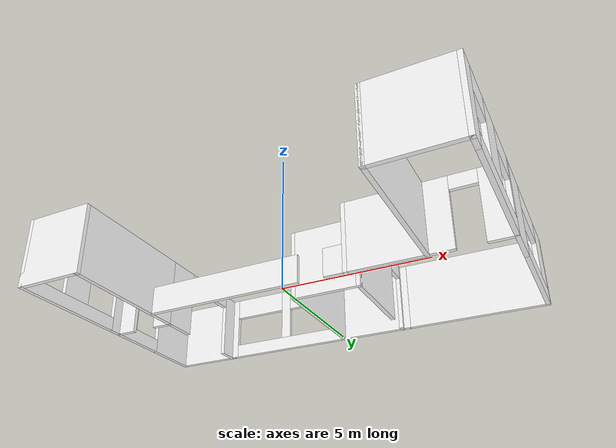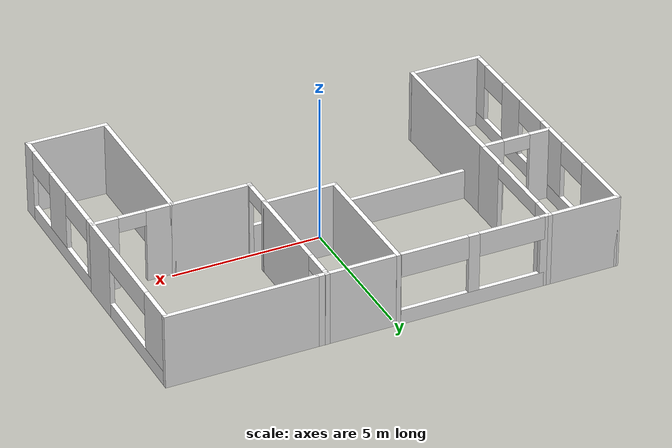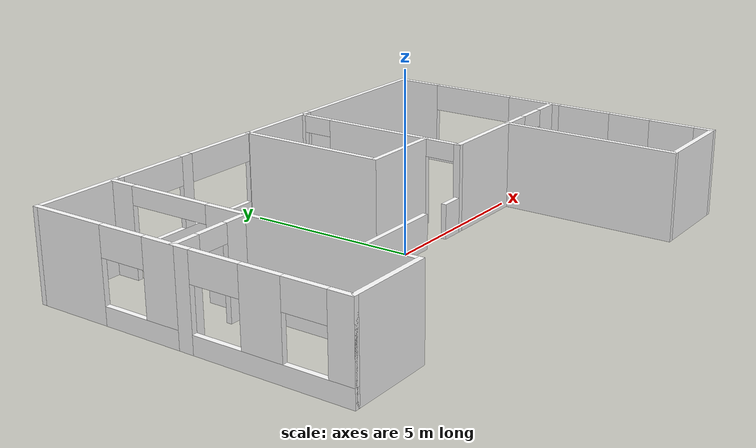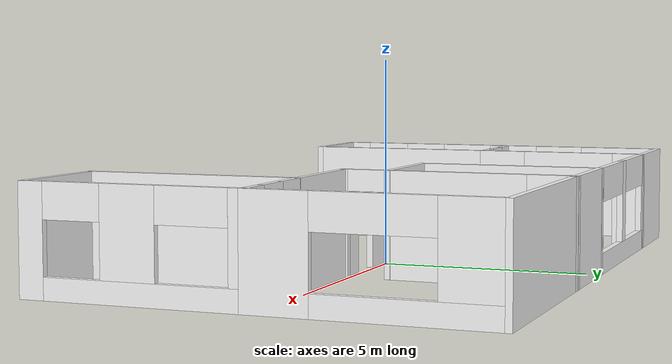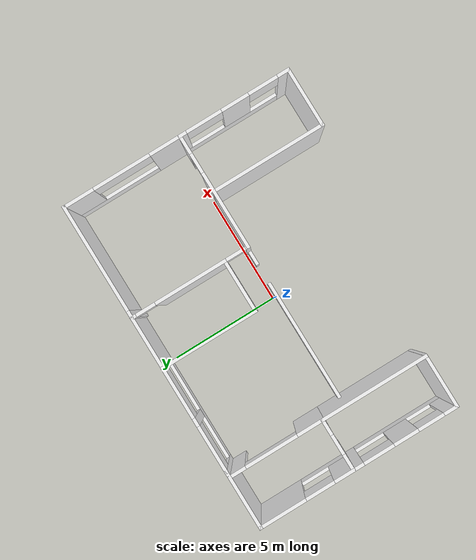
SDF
<sdf version='1.6'>
  <model name='turtlebot3_house'>
    <link name='Wall_101'>
      <pose frame=''>-0.05 3.1 0 0 0 -1.5708</pose>
      <self_collide>0</self_collide>
      <kinematic>0</kinematic>
      <visual name='Wall_101_Visual'>
        <pose frame=''>0 0 1.25 0 -0 0</pose>
        <geometry>
          <box>
            <size>4.5 0.15 2.5</size>
          </box>
        </geometry>
        <material>
	        <diffuse>1.0 1.0 1.0</diffuse>
          <specular>1.0 1.0 1.0</specular>
          <ambient>1.0 1.0 1.0</ambient>
	        <pbr>
	          <metal>
	            <albedo_map>model://wall/materials/textures/grey_wall.png</albedo_map>
	          </metal>
	        </pbr>
          </material>
        <cast_shadows>1</cast_shadows>
        <transparency>0</transparency>
      </visual>
      <collision name='Wall_101_Collision'>
        <laser_retro>0</laser_retro>
        <max_contacts>10</max_contacts>
        <pose frame=''>0 0 1.25 0 -0 0</pose>
        <geometry>
          <box>
            <size>4.5 0.15 2.5</size>
          </box>
        </geometry>
        <surface>
          <friction>
            <ode>
              <mu>1</mu>
              <mu2>1</mu2>
              <fdir1>0 0 0</fdir1>
              <slip1>0</slip1>
              <slip2>0</slip2>
            </ode>
            <torsional>
              <coefficient>1</coefficient>
              <patch_radius>0</patch_radius>
              <surface_radius>0</surface_radius>
              <use_patch_radius>1</use_patch_radius>
              <ode>
                <slip>0</slip>
              </ode>
            </torsional>
          </friction>
          <bounce>
            <restitution_coefficient>0</restitution_coefficient>
            <threshold>1e+06</threshold>
          </bounce>
          <contact>
            <collide_without_contact>0</collide_without_contact>
            <collide_without_contact_bitmask>1</collide_without_contact_bitmask>
            <collide_bitmask>1</collide_bitmask>
            <ode>
              <soft_cfm>0</soft_cfm>
              <soft_erp>0.2</soft_erp>
              <kp>1e+13</kp>
              <kd>1</kd>
              <max_vel>0.01</max_vel>
              <min_depth>0</min_depth>
            </ode>
            <bullet>
              <split_impulse>1</split_impulse>
              <split_impulse_penetration_threshold>-0.01</split_impulse_penetration_threshold>
              <soft_cfm>0</soft_cfm>
              <soft_erp>0.2</soft_erp>
              <kp>1e+13</kp>
              <kd>1</kd>
            </bullet>
          </contact>
        </surface>
      </collision>
    </link>
    <link name='Wall_104'>
      <pose frame=''>2.3 3.1 0 0 -0 1.5708</pose>
      <self_collide>0</self_collide>
      <kinematic>0</kinematic>
      <visual name='Wall_104_Visual_1'>
        <pose frame=''>2.11625 0 1.25 0 -0 0</pose>
        <geometry>
          <box>
            <size>0.267504 0.15 2.5</size>
          </box>
        </geometry>
        <material>
          <pbr>
	          <metal>
	            <albedo_map>model://wall/materials/textures/wood.jpg</albedo_map>
	          </metal>
	        </pbr>
          <diffuse>1.0 1.0 1.0</diffuse>
          <specular>1.0 1.0 1.0</specular>
          <ambient>1.0 1.0 1.0</ambient>
        </material>
        <cast_shadows>1</cast_shadows>
        <transparency>0</transparency>
      </visual>
      <visual name='Wall_104_Visual_2'>
        <pose frame=''>1.5325 0 2.25 0 -0 0</pose>
        <geometry>
          <box>
            <size>0.9 0.15 0.5</size>
          </box>
        </geometry>
        <material>
          <pbr>
	          <metal>
	            <albedo_map>model://wall/materials/textures/wood.jpg</albedo_map>
	          </metal>
	        </pbr>
          <ambient>1 1 1 1</ambient>
          <diffuse>1 1 1 1</diffuse>
          <specular>0.2 0.2 0.2 1</specular>
          <emissive>0 0 0 1</emissive>
        </material>
        <cast_shadows>1</cast_shadows>
        <transparency>0</transparency>
      </visual>
      <visual name='Wall_104_Visual_0'>
        <pose frame=''>-0.583752 0 1.25 0 -0 0</pose>
        <geometry>
          <box>
            <size>3.3325 0.15 2.5</size>
          </box>
        </geometry>
        <material>
          <pbr>
	          <metal>
	            <albedo_map>model://wall/materials/textures/wood.jpg</albedo_map>
	          </metal>
	        </pbr>
          <ambient>1 1 1 1</ambient>
          <diffuse>1 1 1 1</diffuse>
          <specular>0.2 0.2 0.2 1</specular>
          <emissive>0 0 0 1</emissive>
        </material>
        <cast_shadows>1</cast_shadows>
        <transparency>0</transparency>
      </visual>
      <collision name='Wall_104_Collision_1'>
        <laser_retro>0</laser_retro>
        <max_contacts>10</max_contacts>
        <pose frame=''>2.11625 0 1.25 0 -0 0</pose>
        <geometry>
          <box>
            <size>0.267504 0.15 2.5</size>
          </box>
        </geometry>
        <surface>
          <friction>
            <ode>
              <mu>1</mu>
              <mu2>1</mu2>
              <fdir1>0 0 0</fdir1>
              <slip1>0</slip1>
              <slip2>0</slip2>
            </ode>
            <torsional>
              <coefficient>1</coefficient>
              <patch_radius>0</patch_radius>
              <surface_radius>0</surface_radius>
              <use_patch_radius>1</use_patch_radius>
              <ode>
                <slip>0</slip>
              </ode>
            </torsional>
          </friction>
          <bounce>
            <restitution_coefficient>0</restitution_coefficient>
            <threshold>1e+06</threshold>
          </bounce>
          <contact>
            <collide_without_contact>0</collide_without_contact>
            <collide_without_contact_bitmask>1</collide_without_contact_bitmask>
            <collide_bitmask>1</collide_bitmask>
            <ode>
              <soft_cfm>0</soft_cfm>
              <soft_erp>0.2</soft_erp>
              <kp>1e+13</kp>
              <kd>1</kd>
              <max_vel>0.01</max_vel>
              <min_depth>0</min_depth>
            </ode>
            <bullet>
              <split_impulse>1</split_impulse>
              <split_impulse_penetration_threshold>-0.01</split_impulse_penetration_threshold>
              <soft_cfm>0</soft_cfm>
              <soft_erp>0.2</soft_erp>
              <kp>1e+13</kp>
              <kd>1</kd>
            </bullet>
          </contact>
        </surface>
      </collision>
      <collision name='Wall_104_Collision_2'>
        <laser_retro>0</laser_retro>
        <max_contacts>10</max_contacts>
        <pose frame=''>1.5325 0 2.25 0 -0 0</pose>
        <geometry>
          <box>
            <size>0.9 0.15 0.5</size>
          </box>
        </geometry>
        <surface>
          <friction>
            <ode>
              <mu>1</mu>
              <mu2>1</mu2>
              <fdir1>0 0 0</fdir1>
              <slip1>0</slip1>
              <slip2>0</slip2>
            </ode>
            <torsional>
              <coefficient>1</coefficient>
              <patch_radius>0</patch_radius>
              <surface_radius>0</surface_radius>
              <use_patch_radius>1</use_patch_radius>
              <ode>
                <slip>0</slip>
              </ode>
            </torsional>
          </friction>
          <bounce>
            <restitution_coefficient>0</restitution_coefficient>
            <threshold>1e+06</threshold>
          </bounce>
          <contact>
            <collide_without_contact>0</collide_without_contact>
            <collide_without_contact_bitmask>1</collide_without_contact_bitmask>
            <collide_bitmask>1</collide_bitmask>
            <ode>
              <soft_cfm>0</soft_cfm>
              <soft_erp>0.2</soft_erp>
              <kp>1e+13</kp>
              <kd>1</kd>
              <max_vel>0.01</max_vel>
              <min_depth>0</min_depth>
            </ode>
            <bullet>
              <split_impulse>1</split_impulse>
              <split_impulse_penetration_threshold>-0.01</split_impulse_penetration_threshold>
              <soft_cfm>0</soft_cfm>
              <soft_erp>0.2</soft_erp>
              <kp>1e+13</kp>
              <kd>1</kd>
            </bullet>
          </contact>
        </surface>
      </collision>
      <collision name='Wall_104_Collision_0'>
        <laser_retro>0</laser_retro>
        <max_contacts>10</max_contacts>
        <pose frame=''>-0.583752 0 1.25 0 -0 0</pose>
        <geometry>
          <box>
            <size>3.3325 0.15 2.5</size>
          </box>
        </geometry>
        <surface>
          <friction>
            <ode>
              <mu>1</mu>
              <mu2>1</mu2>
              <fdir1>0 0 0</fdir1>
              <slip1>0</slip1>
              <slip2>0</slip2>
            </ode>
            <torsional>
              <coefficient>1</coefficient>
              <patch_radius>0</patch_radius>
              <surface_radius>0</surface_radius>
              <use_patch_radius>1</use_patch_radius>
              <ode>
                <slip>0</slip>
              </ode>
            </torsional>
          </friction>
          <bounce>
            <restitution_coefficient>0</restitution_coefficient>
            <threshold>1e+06</threshold>
          </bounce>
          <contact>
            <collide_without_contact>0</collide_without_contact>
            <collide_without_contact_bitmask>1</collide_without_contact_bitmask>
            <collide_bitmask>1</collide_bitmask>
            <ode>
              <soft_cfm>0</soft_cfm>
              <soft_erp>0.2</soft_erp>
              <kp>1e+13</kp>
              <kd>1</kd>
              <max_vel>0.01</max_vel>
              <min_depth>0</min_depth>
            </ode>
            <bullet>
              <split_impulse>1</split_impulse>
              <split_impulse_penetration_threshold>-0.01</split_impulse_penetration_threshold>
              <soft_cfm>0</soft_cfm>
              <soft_erp>0.2</soft_erp>
              <kp>1e+13</kp>
              <kd>1</kd>
            </bullet>
          </contact>
        </surface>
      </collision>
    </link>
    <link name='Wall_106'>
      <pose frame=''>6.2 -0.175 0 0 -0 0</pose>
      <self_collide>0</self_collide>
      <kinematic>0</kinematic>
      <visual name='Wall_106_Visual_1'>
        <pose frame=''>0.922235 0 1.25 0 -0 0</pose>
        <geometry>
          <box>
            <size>0.905529 0.15 2.5</size>
          </box>
        </geometry>
        <material>
	        <diffuse>1.0 1.0 1.0</diffuse>
          <specular>1.0 1.0 1.0</specular>
          <ambient>1.0 1.0 1.0</ambient>
	        <pbr>
	          <metal>
	            <albedo_map>model://wall/materials/textures/concrete_wall.jpg</albedo_map>
	          </metal>
	        </pbr>
          </material>
        <cast_shadows>1</cast_shadows>
        <transparency>0</transparency>
      </visual>
      <visual name='Wall_106_Visual_2'>
        <pose frame=''>0.019471 0 2.25 0 -0 0</pose>
        <geometry>
          <box>
            <size>0.9 0.15 0.5</size>
          </box>
        </geometry>
        <material>
	        <diffuse>1.0 1.0 1.0</diffuse>
          <specular>1.0 1.0 1.0</specular>
          <ambient>1.0 1.0 1.0</ambient>
	        <pbr>
	          <metal>
	            <albedo_map>model://wall/materials/textures/concrete_wall.jpg</albedo_map>
	          </metal>
	        </pbr>
          </material>
        <cast_shadows>1</cast_shadows>
        <transparency>0</transparency>
      </visual>
      <visual name='Wall_106_Visual_0'>
        <pose frame=''>-0.902765 0 1.25 0 -0 0</pose>
        <geometry>
          <box>
            <size>0.944471 0.15 2.5</size>
          </box>
        </geometry>
        <material>
	        <diffuse>1.0 1.0 1.0</diffuse>
          <specular>1.0 1.0 1.0</specular>
          <ambient>1.0 1.0 1.0</ambient>
	        <pbr>
	          <metal>
	            <albedo_map>model://wall/materials/textures/concrete_wall.jpg</albedo_map>
	          </metal>
	        </pbr>
          </material>
        <cast_shadows>1</cast_shadows>
        <transparency>0</transparency>
      </visual>
      <collision name='Wall_106_Collision_1'>
        <laser_retro>0</laser_retro>
        <max_contacts>10</max_contacts>
        <pose frame=''>0.922235 0 1.25 0 -0 0</pose>
        <geometry>
          <box>
            <size>0.905529 0.15 2.5</size>
          </box>
        </geometry>
        <surface>
          <friction>
            <ode>
              <mu>1</mu>
              <mu2>1</mu2>
              <fdir1>0 0 0</fdir1>
              <slip1>0</slip1>
              <slip2>0</slip2>
            </ode>
            <torsional>
              <coefficient>1</coefficient>
              <patch_radius>0</patch_radius>
              <surface_radius>0</surface_radius>
              <use_patch_radius>1</use_patch_radius>
              <ode>
                <slip>0</slip>
              </ode>
            </torsional>
          </friction>
          <bounce>
            <restitution_coefficient>0</restitution_coefficient>
            <threshold>1e+06</threshold>
          </bounce>
          <contact>
            <collide_without_contact>0</collide_without_contact>
            <collide_without_contact_bitmask>1</collide_without_contact_bitmask>
            <collide_bitmask>1</collide_bitmask>
            <ode>
              <soft_cfm>0</soft_cfm>
              <soft_erp>0.2</soft_erp>
              <kp>1e+13</kp>
              <kd>1</kd>
              <max_vel>0.01</max_vel>
              <min_depth>0</min_depth>
            </ode>
            <bullet>
              <split_impulse>1</split_impulse>
              <split_impulse_penetration_threshold>-0.01</split_impulse_penetration_threshold>
              <soft_cfm>0</soft_cfm>
              <soft_erp>0.2</soft_erp>
              <kp>1e+13</kp>
              <kd>1</kd>
            </bullet>
          </contact>
        </surface>
      </collision>
      <collision name='Wall_106_Collision_0'>
        <laser_retro>0</laser_retro>
        <max_contacts>10</max_contacts>
        <pose frame=''>-0.902765 0 1.25 0 -0 0</pose>
        <geometry>
          <box>
            <size>0.944471 0.15 2.5</size>
          </box>
        </geometry>
        <surface>
          <friction>
            <ode>
              <mu>1</mu>
              <mu2>1</mu2>
              <fdir1>0 0 0</fdir1>
              <slip1>0</slip1>
              <slip2>0</slip2>
            </ode>
            <torsional>
              <coefficient>1</coefficient>
              <patch_radius>0</patch_radius>
              <surface_radius>0</surface_radius>
              <use_patch_radius>1</use_patch_radius>
              <ode>
                <slip>0</slip>
              </ode>
            </torsional>
          </friction>
          <bounce>
            <restitution_coefficient>0</restitution_coefficient>
            <threshold>1e+06</threshold>
          </bounce>
          <contact>
            <collide_without_contact>0</collide_without_contact>
            <collide_without_contact_bitmask>1</collide_without_contact_bitmask>
            <collide_bitmask>1</collide_bitmask>
            <ode>
              <soft_cfm>0</soft_cfm>
              <soft_erp>0.2</soft_erp>
              <kp>1e+13</kp>
              <kd>1</kd>
              <max_vel>0.01</max_vel>
              <min_depth>0</min_depth>
            </ode>
            <bullet>
              <split_impulse>1</split_impulse>
              <split_impulse_penetration_threshold>-0.01</split_impulse_penetration_threshold>
              <soft_cfm>0</soft_cfm>
              <soft_erp>0.2</soft_erp>
              <kp>1e+13</kp>
              <kd>1</kd>
            </bullet>
          </contact>
        </surface>
      </collision>
      <collision name='Wall_106_Collision_2'>
        <laser_retro>0</laser_retro>
        <max_contacts>10</max_contacts>
        <pose frame=''>0.019471 0 2.25 0 -0 0</pose>
        <geometry>
          <box>
            <size>0.9 0.15 0.5</size>
          </box>
        </geometry>
        <surface>
          <friction>
            <ode>
              <mu>1</mu>
              <mu2>1</mu2>
              <fdir1>0 0 0</fdir1>
              <slip1>0</slip1>
              <slip2>0</slip2>
            </ode>
            <torsional>
              <coefficient>1</coefficient>
              <patch_radius>0</patch_radius>
              <surface_radius>0</surface_radius>
              <use_patch_radius>1</use_patch_radius>
              <ode>
                <slip>0</slip>
              </ode>
            </torsional>
          </friction>
          <bounce>
            <restitution_coefficient>0</restitution_coefficient>
            <threshold>1e+06</threshold>
          </bounce>
          <contact>
            <collide_without_contact>0</collide_without_contact>
            <collide_without_contact_bitmask>1</collide_without_contact_bitmask>
            <collide_bitmask>1</collide_bitmask>
            <ode>
              <soft_cfm>0</soft_cfm>
              <soft_erp>0.2</soft_erp>
              <kp>1e+13</kp>
              <kd>1</kd>
              <max_vel>0.01</max_vel>
              <min_depth>0</min_depth>
            </ode>
            <bullet>
              <split_impulse>1</split_impulse>
              <split_impulse_penetration_threshold>-0.01</split_impulse_penetration_threshold>
              <soft_cfm>0</soft_cfm>
              <soft_erp>0.2</soft_erp>
              <kp>1e+13</kp>
              <kd>1</kd>
            </bullet>
          </contact>
        </surface>
      </collision>
    </link>
    <link name='Wall_108'>
      <pose frame=''>-1.37512 -0.17488 0 0 -0 0</pose>
      <self_collide>0</self_collide>
      <kinematic>0</kinematic>
      <visual name='Wall_108_Visual_0'>
        <pose frame=''>-0.856324 0 0.5 0 -0 0</pose>
        <geometry>
          <box>
            <size>5.78735 0.15 1</size>
          </box>
        </geometry>
        <material>
	        <diffuse>1.0 1.0 1.0</diffuse>
          <specular>1.0 1.0 1.0</specular>
          <ambient>1.0 1.0 1.0</ambient>
	        <pbr>
	          <metal>
	            <albedo_map>model://wall/materials/textures/stone_wall_repeat.jpg</albedo_map>
	          </metal>
	        </pbr>
          </material>
        <cast_shadows>1</cast_shadows>
        <transparency>0</transparency>
      </visual>
      <visual name='Wall_108_Visual_1'>
        <pose frame=''>3.34368 0 0.5 0 -0 0</pose>
        <geometry>
          <box>
            <size>0.812647 0.15 1</size>
          </box>
        </geometry>
        <material>
	        <diffuse>1.0 1.0 1.0</diffuse>
          <specular>1.0 1.0 1.0</specular>
          <ambient>1.0 1.0 1.0</ambient>
	        <pbr>
	          <metal>
	            <albedo_map>model://wall/materials/textures/stone_wall.jpg</albedo_map>
	          </metal>
	        </pbr>
          </material>
        <cast_shadows>1</cast_shadows>
        <transparency>0</transparency>
      </visual>
      <collision name='Wall_108_Collision_1'>
        <laser_retro>0</laser_retro>
        <max_contacts>10</max_contacts>
        <pose frame=''>3.34368 0 0.5 0 -0 0</pose>
        <geometry>
          <box>
            <size>0.812647 0.15 1</size>
          </box>
        </geometry>
        <surface>
          <friction>
            <ode>
              <mu>1</mu>
              <mu2>1</mu2>
              <fdir1>0 0 0</fdir1>
              <slip1>0</slip1>
              <slip2>0</slip2>
            </ode>
            <torsional>
              <coefficient>1</coefficient>
              <patch_radius>0</patch_radius>
              <surface_radius>0</surface_radius>
              <use_patch_radius>1</use_patch_radius>
              <ode>
                <slip>0</slip>
              </ode>
            </torsional>
          </friction>
          <bounce>
            <restitution_coefficient>0</restitution_coefficient>
            <threshold>1e+06</threshold>
          </bounce>
          <contact>
            <collide_without_contact>0</collide_without_contact>
            <collide_without_contact_bitmask>1</collide_without_contact_bitmask>
            <collide_bitmask>1</collide_bitmask>
            <ode>
              <soft_cfm>0</soft_cfm>
              <soft_erp>0.2</soft_erp>
              <kp>1e+13</kp>
              <kd>1</kd>
              <max_vel>0.01</max_vel>
              <min_depth>0</min_depth>
            </ode>
            <bullet>
              <split_impulse>1</split_impulse>
              <split_impulse_penetration_threshold>-0.01</split_impulse_penetration_threshold>
              <soft_cfm>0</soft_cfm>
              <soft_erp>0.2</soft_erp>
              <kp>1e+13</kp>
              <kd>1</kd>
            </bullet>
          </contact>
        </surface>
      </collision>
      <collision name='Wall_108_Collision_0'>
        <laser_retro>0</laser_retro>
        <max_contacts>10</max_contacts>
        <pose frame=''>-0.856324 0 0.5 0 -0 0</pose>
        <geometry>
          <box>
            <size>5.78735 0.15 1</size>
          </box>
        </geometry>
        <surface>
          <friction>
            <ode>
              <mu>1</mu>
              <mu2>1</mu2>
              <fdir1>0 0 0</fdir1>
              <slip1>0</slip1>
              <slip2>0</slip2>
            </ode>
            <torsional>
              <coefficient>1</coefficient>
              <patch_radius>0</patch_radius>
              <surface_radius>0</surface_radius>
              <use_patch_radius>1</use_patch_radius>
              <ode>
                <slip>0</slip>
              </ode>
            </torsional>
          </friction>
          <bounce>
            <restitution_coefficient>0</restitution_coefficient>
            <threshold>1e+06</threshold>
          </bounce>
          <contact>
            <collide_without_contact>0</collide_without_contact>
            <collide_without_contact_bitmask>1</collide_without_contact_bitmask>
            <collide_bitmask>1</collide_bitmask>
            <ode>
              <soft_cfm>0</soft_cfm>
              <soft_erp>0.2</soft_erp>
              <kp>1e+13</kp>
              <kd>1</kd>
              <max_vel>0.01</max_vel>
              <min_depth>0</min_depth>
            </ode>
            <bullet>
              <split_impulse>1</split_impulse>
              <split_impulse_penetration_threshold>-0.01</split_impulse_penetration_threshold>
              <soft_cfm>0</soft_cfm>
              <soft_erp>0.2</soft_erp>
              <kp>1e+13</kp>
              <kd>1</kd>
            </bullet>
          </contact>
        </surface>
      </collision>
    </link>
    <link name='Wall_81'>
      <pose frame=''>5.07752 5.2688 0 0 -0 3.14159</pose>
      <self_collide>0</self_collide>
      <kinematic>0</kinematic>
      <visual name='Wall_81_Visual'>
        <pose frame=''>0 0 1.25 0 -0 0</pose>
        <geometry>
          <box>
            <size>5 0.15 2.5</size>
          </box>
        </geometry>
        <material>
	        <diffuse>1.0 1.0 1.0</diffuse>
          <specular>1.0 1.0 1.0</specular>
          <ambient>1.0 1.0 1.0</ambient>
	        <pbr>
	          <metal>
	            <albedo_map>model://wall/materials/textures/concrete_wall.jpg</albedo_map>
	          </metal>
	        </pbr>
          </material>
        <cast_shadows>1</cast_shadows>
        <transparency>0</transparency>
      </visual>
      <collision name='Wall_81_Collision'>
        <laser_retro>0</laser_retro>
        <max_contacts>10</max_contacts>
        <pose frame=''>0 0 1.25 0 -0 0</pose>
        <geometry>
          <box>
            <size>5 0.15 2.5</size>
          </box>
        </geometry>
        <surface>
          <friction>
            <ode>
              <mu>1</mu>
              <mu2>1</mu2>
              <fdir1>0 0 0</fdir1>
              <slip1>0</slip1>
              <slip2>0</slip2>
            </ode>
            <torsional>
              <coefficient>1</coefficient>
              <patch_radius>0</patch_radius>
              <surface_radius>0</surface_radius>
              <use_patch_radius>1</use_patch_radius>
              <ode>
                <slip>0</slip>
              </ode>
            </torsional>
          </friction>
          <bounce>
            <restitution_coefficient>0</restitution_coefficient>
            <threshold>1e+06</threshold>
          </bounce>
          <contact>
            <collide_without_contact>0</collide_without_contact>
            <collide_without_contact_bitmask>1</collide_without_contact_bitmask>
            <collide_bitmask>1</collide_bitmask>
            <ode>
              <soft_cfm>0</soft_cfm>
              <soft_erp>0.2</soft_erp>
              <kp>1e+13</kp>
              <kd>1</kd>
              <max_vel>0.01</max_vel>
              <min_depth>0</min_depth>
            </ode>
            <bullet>
              <split_impulse>1</split_impulse>
              <split_impulse_penetration_threshold>-0.01</split_impulse_penetration_threshold>
              <soft_cfm>0</soft_cfm>
              <soft_erp>0.2</soft_erp>
              <kp>1e+13</kp>
              <kd>1</kd>
            </bullet>
          </contact>
        </surface>
      </collision>
    </link>
    <link name='Wall_82'>
      <pose frame=''>1.25 5.26876 0 0 -0 3.14159</pose>
      <self_collide>0</self_collide>
      <kinematic>0</kinematic>
      <visual name='Wall_82_Visual'>
        <pose frame=''>0 0 1.25 0 -0 0</pose>
        <geometry>
          <box>
            <size>2.75 0.15 2.5</size>
          </box>
        </geometry>
        <material>
	        <diffuse>1.0 1.0 1.0</diffuse>
          <specular>1.0 1.0 1.0</specular>
          <ambient>1.0 1.0 1.0</ambient>
	        <pbr>
	          <metal>
	            <albedo_map>model://wall/materials/textures/concrete_wall.jpg</albedo_map>
	          </metal>
	        </pbr>
          </material>
        <cast_shadows>1</cast_shadows>
        <transparency>0</transparency>
      </visual>
      <collision name='Wall_82_Collision'>
        <laser_retro>0</laser_retro>
        <max_contacts>10</max_contacts>
        <pose frame=''>0 0 1.25 0 -0 0</pose>
        <geometry>
          <box>
            <size>2.75 0.15 2.5</size>
          </box>
        </geometry>
        <surface>
          <friction>
            <ode>
              <mu>1</mu>
              <mu2>1</mu2>
              <fdir1>0 0 0</fdir1>
              <slip1>0</slip1>
              <slip2>0</slip2>
            </ode>
            <torsional>
              <coefficient>1</coefficient>
              <patch_radius>0</patch_radius>
              <surface_radius>0</surface_radius>
              <use_patch_radius>1</use_patch_radius>
              <ode>
                <slip>0</slip>
              </ode>
            </torsional>
          </friction>
          <bounce>
            <restitution_coefficient>0</restitution_coefficient>
            <threshold>1e+06</threshold>
          </bounce>
          <contact>
            <collide_without_contact>0</collide_without_contact>
            <collide_without_contact_bitmask>1</collide_without_contact_bitmask>
            <collide_bitmask>1</collide_bitmask>
            <ode>
              <soft_cfm>0</soft_cfm>
              <soft_erp>0.2</soft_erp>
              <kp>1e+13</kp>
              <kd>1</kd>
              <max_vel>0.01</max_vel>
              <min_depth>0</min_depth>
            </ode>
            <bullet>
              <split_impulse>1</split_impulse>
              <split_impulse_penetration_threshold>-0.01</split_impulse_penetration_threshold>
              <soft_cfm>0</soft_cfm>
              <soft_erp>0.2</soft_erp>
              <kp>1e+13</kp>
              <kd>1</kd>
            </bullet>
          </contact>
        </surface>
      </collision>
    </link>
    <link name='Wall_83'>
      <pose frame=''>-2.475 5.275 0 0 -0 3.14159</pose>
      <self_collide>0</self_collide>
      <kinematic>0</kinematic>
      <visual name='Wall_83_Visual_2'>
        <pose frame=''>0.110246 0 1.5 0 -0 0</pose>
        <geometry>
          <box>
            <size>0.37052 0.15 2</size>
          </box>
        </geometry>
        <material>
	        <diffuse>1.0 1.0 1.0</diffuse>
          <specular>1.0 1.0 1.0</specular>
          <ambient>1.0 1.0 1.0</ambient>
	        <pbr>
	          <metal>
	            <albedo_map>model://wall/materials/textures/orange_wall.jpg</albedo_map>
	          </metal>
	        </pbr>
          </material>
        <cast_shadows>1</cast_shadows>
        <transparency>0</transparency>
      </visual>
      <visual name='Wall_83_Visual_6'>
        <pose frame=''>1.39775 0 2.1 0 -0 0</pose>
        <geometry>
          <box>
            <size>2.20449 0.15 0.8</size>
          </box>
        </geometry>
        <material>
	        <diffuse>1.0 1.0 1.0</diffuse>
          <specular>1.0 1.0 1.0</specular>
          <ambient>1.0 1.0 1.0</ambient>
	        <pbr>
	          <metal>
	            <albedo_map>model://wall/materials/textures/orange_wall.jpg</albedo_map>
	          </metal>
	        </pbr>
          </material>
        <cast_shadows>1</cast_shadows>
        <transparency>0</transparency>
      </visual>
      <visual name='Wall_83_Visual_3'>
        <pose frame=''>0.110246 0 1.5 0 -0 0</pose>
        <geometry>
          <box>
            <size>0.37052 0.15 2</size>
          </box>
        </geometry>
        <material>
	        <diffuse>1.0 1.0 1.0</diffuse>
          <specular>1.0 1.0 1.0</specular>
          <ambient>1.0 1.0 1.0</ambient>
	        <pbr>
	          <metal>
	            <albedo_map>model://wall/materials/textures/orange_wall.jpg</albedo_map>
	          </metal>
	        </pbr>
          </material>
        <cast_shadows>1</cast_shadows>
        <transparency>0</transparency>
      </visual>
      <visual name='Wall_83_Visual_1'>
        <pose frame=''>0.080993 0 0.25 0 -0 0</pose>
        <geometry>
          <box>
            <size>4.83801 0.15 0.5</size>
          </box>
        </geometry>
       <material>
	        <diffuse>1.0 1.0 1.0</diffuse>
          <specular>1.0 1.0 1.0</specular>
          <ambient>1.0 1.0 1.0</ambient>
	        <pbr>
	          <metal>
	            <albedo_map>model://wall/materials/textures/orange_wall.jpg</albedo_map>
	          </metal>
	        </pbr>
          </material>
        <cast_shadows>1</cast_shadows>
        <transparency>0</transparency>
      </visual>
      <visual name='Wall_83_Visual_4'>
        <pose frame=''>-1.20651 0 2.1 0 -0 0</pose>
        <geometry>
          <box>
            <size>2.263 0.15 0.8</size>
          </box>
        </geometry>
        <material>
	        <diffuse>1.0 1.0 1.0</diffuse>
          <specular>1.0 1.0 1.0</specular>
          <ambient>1.0 1.0 1.0</ambient>
	        <pbr>
	          <metal>
	            <albedo_map>model://wall/materials/textures/orange_wall.jpg</albedo_map>
	          </metal>
	        </pbr>
          </material>
        <cast_shadows>1</cast_shadows>
        <transparency>0</transparency>
      </visual>
      <visual name='Wall_83_Visual_5'>
        <pose frame=''>1.39775 0 2.1 0 -0 0</pose>
        <geometry>
          <box>
            <size>2.20449 0.15 0.8</size>
          </box>
        </geometry>
       <material>
	        <diffuse>1.0 1.0 1.0</diffuse>
          <specular>1.0 1.0 1.0</specular>
          <ambient>1.0 1.0 1.0</ambient>
	        <pbr>
	          <metal>
	            <albedo_map>model://wall/materials/textures/orange_wall.jpg</albedo_map>
	          </metal>
	        </pbr>
          </material>
        <cast_shadows>1</cast_shadows>
        <transparency>0</transparency>
      </visual>
      <visual name='Wall_83_Visual_0'>
        <pose frame=''>-2.41901 0 1.25 0 -0 0</pose>
        <geometry>
          <box>
            <size>0.161986 0.15 2.5</size>
          </box>
        </geometry>
        <material>
	        <diffuse>1.0 1.0 1.0</diffuse>
          <specular>1.0 1.0 1.0</specular>
          <ambient>1.0 1.0 1.0</ambient>
	        <pbr>
	          <metal>
	            <albedo_map>model://wall/materials/textures/orange_wall.jpg</albedo_map>
	          </metal>
	        </pbr>
          </material>
        <cast_shadows>1</cast_shadows>
        <transparency>0</transparency>
      </visual>
      <collision name='Wall_83_Collision_4'>
        <laser_retro>0</laser_retro>
        <max_contacts>10</max_contacts>
        <pose frame=''>-1.20651 0 2.1 0 -0 0</pose>
        <geometry>
          <box>
            <size>2.263 0.15 0.8</size>
          </box>
        </geometry>
        <surface>
          <friction>
            <ode>
              <mu>1</mu>
              <mu2>1</mu2>
              <fdir1>0 0 0</fdir1>
              <slip1>0</slip1>
              <slip2>0</slip2>
            </ode>
            <torsional>
              <coefficient>1</coefficient>
              <patch_radius>0</patch_radius>
              <surface_radius>0</surface_radius>
              <use_patch_radius>1</use_patch_radius>
              <ode>
                <slip>0</slip>
              </ode>
            </torsional>
          </friction>
          <bounce>
            <restitution_coefficient>0</restitution_coefficient>
            <threshold>1e+06</threshold>
          </bounce>
          <contact>
            <collide_without_contact>0</collide_without_contact>
            <collide_without_contact_bitmask>1</collide_without_contact_bitmask>
            <collide_bitmask>1</collide_bitmask>
            <ode>
              <soft_cfm>0</soft_cfm>
              <soft_erp>0.2</soft_erp>
              <kp>1e+13</kp>
              <kd>1</kd>
              <max_vel>0.01</max_vel>
              <min_depth>0</min_depth>
            </ode>
            <bullet>
              <split_impulse>1</split_impulse>
              <split_impulse_penetration_threshold>-0.01</split_impulse_penetration_threshold>
              <soft_cfm>0</soft_cfm>
              <soft_erp>0.2</soft_erp>
              <kp>1e+13</kp>
              <kd>1</kd>
            </bullet>
          </contact>
        </surface>
      </collision>
      <collision name='Wall_83_Collision_2'>
        <laser_retro>0</laser_retro>
        <max_contacts>10</max_contacts>
        <pose frame=''>0.110246 0 1.5 0 -0 0</pose>
        <geometry>
          <box>
            <size>0.37052 0.15 2</size>
          </box>
        </geometry>
        <surface>
          <friction>
            <ode>
              <mu>1</mu>
              <mu2>1</mu2>
              <fdir1>0 0 0</fdir1>
              <slip1>0</slip1>
              <slip2>0</slip2>
            </ode>
            <torsional>
              <coefficient>1</coefficient>
              <patch_radius>0</patch_radius>
              <surface_radius>0</surface_radius>
              <use_patch_radius>1</use_patch_radius>
              <ode>
                <slip>0</slip>
              </ode>
            </torsional>
          </friction>
          <bounce>
            <restitution_coefficient>0</restitution_coefficient>
            <threshold>1e+06</threshold>
          </bounce>
          <contact>
            <collide_without_contact>0</collide_without_contact>
            <collide_without_contact_bitmask>1</collide_without_contact_bitmask>
            <collide_bitmask>1</collide_bitmask>
            <ode>
              <soft_cfm>0</soft_cfm>
              <soft_erp>0.2</soft_erp>
              <kp>1e+13</kp>
              <kd>1</kd>
              <max_vel>0.01</max_vel>
              <min_depth>0</min_depth>
            </ode>
            <bullet>
              <split_impulse>1</split_impulse>
              <split_impulse_penetration_threshold>-0.01</split_impulse_penetration_threshold>
              <soft_cfm>0</soft_cfm>
              <soft_erp>0.2</soft_erp>
              <kp>1e+13</kp>
              <kd>1</kd>
            </bullet>
          </contact>
        </surface>
      </collision>
      <collision name='Wall_83_Collision_6'>
        <laser_retro>0</laser_retro>
        <max_contacts>10</max_contacts>
        <pose frame=''>1.39775 0 2.1 0 -0 0</pose>
        <geometry>
          <box>
            <size>2.20449 0.15 0.8</size>
          </box>
        </geometry>
        <surface>
          <friction>
            <ode>
              <mu>1</mu>
              <mu2>1</mu2>
              <fdir1>0 0 0</fdir1>
              <slip1>0</slip1>
              <slip2>0</slip2>
            </ode>
            <torsional>
              <coefficient>1</coefficient>
              <patch_radius>0</patch_radius>
              <surface_radius>0</surface_radius>
              <use_patch_radius>1</use_patch_radius>
              <ode>
                <slip>0</slip>
              </ode>
            </torsional>
          </friction>
          <bounce>
            <restitution_coefficient>0</restitution_coefficient>
            <threshold>1e+06</threshold>
          </bounce>
          <contact>
            <collide_without_contact>0</collide_without_contact>
            <collide_without_contact_bitmask>1</collide_without_contact_bitmask>
            <collide_bitmask>1</collide_bitmask>
            <ode>
              <soft_cfm>0</soft_cfm>
              <soft_erp>0.2</soft_erp>
              <kp>1e+13</kp>
              <kd>1</kd>
              <max_vel>0.01</max_vel>
              <min_depth>0</min_depth>
            </ode>
            <bullet>
              <split_impulse>1</split_impulse>
              <split_impulse_penetration_threshold>-0.01</split_impulse_penetration_threshold>
              <soft_cfm>0</soft_cfm>
              <soft_erp>0.2</soft_erp>
              <kp>1e+13</kp>
              <kd>1</kd>
            </bullet>
          </contact>
        </surface>
      </collision>
      <collision name='Wall_83_Collision_0'>
        <laser_retro>0</laser_retro>
        <max_contacts>10</max_contacts>
        <pose frame=''>-2.41901 0 1.25 0 -0 0</pose>
        <geometry>
          <box>
            <size>0.161986 0.15 2.5</size>
          </box>
        </geometry>
        <surface>
          <friction>
            <ode>
              <mu>1</mu>
              <mu2>1</mu2>
              <fdir1>0 0 0</fdir1>
              <slip1>0</slip1>
              <slip2>0</slip2>
            </ode>
            <torsional>
              <coefficient>1</coefficient>
              <patch_radius>0</patch_radius>
              <surface_radius>0</surface_radius>
              <use_patch_radius>1</use_patch_radius>
              <ode>
                <slip>0</slip>
              </ode>
            </torsional>
          </friction>
          <bounce>
            <restitution_coefficient>0</restitution_coefficient>
            <threshold>1e+06</threshold>
          </bounce>
          <contact>
            <collide_without_contact>0</collide_without_contact>
            <collide_without_contact_bitmask>1</collide_without_contact_bitmask>
            <collide_bitmask>1</collide_bitmask>
            <ode>
              <soft_cfm>0</soft_cfm>
              <soft_erp>0.2</soft_erp>
              <kp>1e+13</kp>
              <kd>1</kd>
              <max_vel>0.01</max_vel>
              <min_depth>0</min_depth>
            </ode>
            <bullet>
              <split_impulse>1</split_impulse>
              <split_impulse_penetration_threshold>-0.01</split_impulse_penetration_threshold>
              <soft_cfm>0</soft_cfm>
              <soft_erp>0.2</soft_erp>
              <kp>1e+13</kp>
              <kd>1</kd>
            </bullet>
          </contact>
        </surface>
      </collision>
      <collision name='Wall_83_Collision_1'>
        <laser_retro>0</laser_retro>
        <max_contacts>10</max_contacts>
        <pose frame=''>0.080993 0 0.25 0 -0 0</pose>
        <geometry>
          <box>
            <size>4.83801 0.15 0.5</size>
          </box>
        </geometry>
        <surface>
          <friction>
            <ode>
              <mu>1</mu>
              <mu2>1</mu2>
              <fdir1>0 0 0</fdir1>
              <slip1>0</slip1>
              <slip2>0</slip2>
            </ode>
            <torsional>
              <coefficient>1</coefficient>
              <patch_radius>0</patch_radius>
              <surface_radius>0</surface_radius>
              <use_patch_radius>1</use_patch_radius>
              <ode>
                <slip>0</slip>
              </ode>
            </torsional>
          </friction>
          <bounce>
            <restitution_coefficient>0</restitution_coefficient>
            <threshold>1e+06</threshold>
          </bounce>
          <contact>
            <collide_without_contact>0</collide_without_contact>
            <collide_without_contact_bitmask>1</collide_without_contact_bitmask>
            <collide_bitmask>1</collide_bitmask>
            <ode>
              <soft_cfm>0</soft_cfm>
              <soft_erp>0.2</soft_erp>
              <kp>1e+13</kp>
              <kd>1</kd>
              <max_vel>0.01</max_vel>
              <min_depth>0</min_depth>
            </ode>
            <bullet>
              <split_impulse>1</split_impulse>
              <split_impulse_penetration_threshold>-0.01</split_impulse_penetration_threshold>
              <soft_cfm>0</soft_cfm>
              <soft_erp>0.2</soft_erp>
              <kp>1e+13</kp>
              <kd>1</kd>
            </bullet>
          </contact>
        </surface>
      </collision>
      <collision name='Wall_83_Collision_3'>
        <laser_retro>0</laser_retro>
        <max_contacts>10</max_contacts>
        <pose frame=''>0.110246 0 1.5 0 -0 0</pose>
        <geometry>
          <box>
            <size>0.37052 0.15 2</size>
          </box>
        </geometry>
        <surface>
          <friction>
            <ode>
              <mu>1</mu>
              <mu2>1</mu2>
              <fdir1>0 0 0</fdir1>
              <slip1>0</slip1>
              <slip2>0</slip2>
            </ode>
            <torsional>
              <coefficient>1</coefficient>
              <patch_radius>0</patch_radius>
              <surface_radius>0</surface_radius>
              <use_patch_radius>1</use_patch_radius>
              <ode>
                <slip>0</slip>
              </ode>
            </torsional>
          </friction>
          <bounce>
            <restitution_coefficient>0</restitution_coefficient>
            <threshold>1e+06</threshold>
          </bounce>
          <contact>
            <collide_without_contact>0</collide_without_contact>
            <collide_without_contact_bitmask>1</collide_without_contact_bitmask>
            <collide_bitmask>1</collide_bitmask>
            <ode>
              <soft_cfm>0</soft_cfm>
              <soft_erp>0.2</soft_erp>
              <kp>1e+13</kp>
              <kd>1</kd>
              <max_vel>0.01</max_vel>
              <min_depth>0</min_depth>
            </ode>
            <bullet>
              <split_impulse>1</split_impulse>
              <split_impulse_penetration_threshold>-0.01</split_impulse_penetration_threshold>
              <soft_cfm>0</soft_cfm>
              <soft_erp>0.2</soft_erp>
              <kp>1e+13</kp>
              <kd>1</kd>
            </bullet>
          </contact>
        </surface>
      </collision>
      <collision name='Wall_83_Collision_5'>
        <laser_retro>0</laser_retro>
        <max_contacts>10</max_contacts>
        <pose frame=''>1.39775 0 2.1 0 -0 0</pose>
        <geometry>
          <box>
            <size>2.20449 0.15 0.8</size>
          </box>
        </geometry>
        <surface>
          <friction>
            <ode>
              <mu>1</mu>
              <mu2>1</mu2>
              <fdir1>0 0 0</fdir1>
              <slip1>0</slip1>
              <slip2>0</slip2>
            </ode>
            <torsional>
              <coefficient>1</coefficient>
              <patch_radius>0</patch_radius>
              <surface_radius>0</surface_radius>
              <use_patch_radius>1</use_patch_radius>
              <ode>
                <slip>0</slip>
              </ode>
            </torsional>
          </friction>
          <bounce>
            <restitution_coefficient>0</restitution_coefficient>
            <threshold>1e+06</threshold>
          </bounce>
          <contact>
            <collide_without_contact>0</collide_without_contact>
            <collide_without_contact_bitmask>1</collide_without_contact_bitmask>
            <collide_bitmask>1</collide_bitmask>
            <ode>
              <soft_cfm>0</soft_cfm>
              <soft_erp>0.2</soft_erp>
              <kp>1e+13</kp>
              <kd>1</kd>
              <max_vel>0.01</max_vel>
              <min_depth>0</min_depth>
            </ode>
            <bullet>
              <split_impulse>1</split_impulse>
              <split_impulse_penetration_threshold>-0.01</split_impulse_penetration_threshold>
              <soft_cfm>0</soft_cfm>
              <soft_erp>0.2</soft_erp>
              <kp>1e+13</kp>
              <kd>1</kd>
            </bullet>
          </contact>
        </surface>
      </collision>
    </link>
    <link name='Wall_84'>
      <pose frame=''>-6.2 5.275 0 0 -0 3.14159</pose>
      <self_collide>0</self_collide>
      <kinematic>0</kinematic>
      <visual name='Wall_84_Visual'>
        <pose frame=''>0 0 1.25 0 -0 0</pose>
        <geometry>
          <box>
            <size>2.75 0.15 2.5</size>
          </box>
        </geometry>
       <material>
	        <diffuse>1.0 1.0 1.0</diffuse>
          <specular>1.0 1.0 1.0</specular>
          <ambient>1.0 1.0 1.0</ambient>
	        <pbr>
	          <metal>
	            <albedo_map>model://wall/materials/textures/concrete_wall.jpg</albedo_map>
	          </metal>
	        </pbr>
          </material>
        <cast_shadows>1</cast_shadows>
        <transparency>0</transparency>
      </visual>
      <collision name='Wall_84_Collision'>
        <laser_retro>0</laser_retro>
        <max_contacts>10</max_contacts>
        <pose frame=''>0 0 1.25 0 -0 0</pose>
        <geometry>
          <box>
            <size>2.75 0.15 2.5</size>
          </box>
        </geometry>
        <surface>
          <friction>
            <ode>
              <mu>1</mu>
              <mu2>1</mu2>
              <fdir1>0 0 0</fdir1>
              <slip1>0</slip1>
              <slip2>0</slip2>
            </ode>
            <torsional>
              <coefficient>1</coefficient>
              <patch_radius>0</patch_radius>
              <surface_radius>0</surface_radius>
              <use_patch_radius>1</use_patch_radius>
              <ode>
                <slip>0</slip>
              </ode>
            </torsional>
          </friction>
          <bounce>
            <restitution_coefficient>0</restitution_coefficient>
            <threshold>1e+06</threshold>
          </bounce>
          <contact>
            <collide_without_contact>0</collide_without_contact>
            <collide_without_contact_bitmask>1</collide_without_contact_bitmask>
            <collide_bitmask>1</collide_bitmask>
            <ode>
              <soft_cfm>0</soft_cfm>
              <soft_erp>0.2</soft_erp>
              <kp>1e+13</kp>
              <kd>1</kd>
              <max_vel>0.01</max_vel>
              <min_depth>0</min_depth>
            </ode>
            <bullet>
              <split_impulse>1</split_impulse>
              <split_impulse_penetration_threshold>-0.01</split_impulse_penetration_threshold>
              <soft_cfm>0</soft_cfm>
              <soft_erp>0.2</soft_erp>
              <kp>1e+13</kp>
              <kd>1</kd>
            </bullet>
          </contact>
        </surface>
      </collision>
    </link>
    <link name='Wall_85'>
      <pose frame=''>-7.5 3.1 0 0 0 -1.5708</pose>
      <self_collide>0</self_collide>
      <kinematic>0</kinematic>
      <visual name='Wall_85_Visual_3'>
        <pose frame=''>0.62212 0 2.1 0 -0 0</pose>
        <geometry>
          <box>
            <size>1.332 0.15 0.8</size>
          </box>
        </geometry>
        <material>
	        <diffuse>1.0 1.0 1.0</diffuse>
          <specular>1.0 1.0 1.0</specular>
          <ambient>1.0 1.0 1.0</ambient>
	        <pbr>
	          <metal>
	            <albedo_map>model://wall/materials/textures/concrete_wall.jpg</albedo_map>
	          </metal>
	        </pbr>
          </material>
        <cast_shadows>1</cast_shadows>
        <transparency>0</transparency>
      </visual>
      <visual name='Wall_85_Visual_2'>
        <pose frame=''>1.76906 0 1.5 0 -0 0</pose>
        <geometry>
          <box>
            <size>0.96188 0.15 2</size>
          </box>
        </geometry>
        <material>
	        <diffuse>1.0 1.0 1.0</diffuse>
          <specular>1.0 1.0 1.0</specular>
          <ambient>1.0 1.0 1.0</ambient>
	        <pbr>
	          <metal>
	            <albedo_map>model://wall/materials/textures/concrete_wall.jpg</albedo_map>
	          </metal>
	        </pbr>
          </material>
        <cast_shadows>1</cast_shadows>
        <transparency>0</transparency>
      </visual>
      <visual name='Wall_85_Visual_0'>
        <pose frame=''>-1.14694 0 1.25 0 -0 0</pose>
        <geometry>
          <box>
            <size>2.20612 0.15 2.5</size>
          </box>
        </geometry>
        <material>
	        <diffuse>1.0 1.0 1.0</diffuse>
          <specular>1.0 1.0 1.0</specular>
          <ambient>1.0 1.0 1.0</ambient>
	        <pbr>
	          <metal>
	            <albedo_map>model://wall/materials/textures/concrete_wall.jpg</albedo_map>
	          </metal>
	        </pbr>
          </material>
        <cast_shadows>1</cast_shadows>
        <transparency>0</transparency>
      </visual>
      <visual name='Wall_85_Visual_1'>
        <pose frame=''>1.10306 0 0.25 0 -0 0</pose>
        <geometry>
          <box>
            <size>2.29388 0.15 0.5</size>
          </box>
        </geometry>
        <material>
	        <diffuse>1.0 1.0 1.0</diffuse>
          <specular>1.0 1.0 1.0</specular>
          <ambient>1.0 1.0 1.0</ambient>
	        <pbr>
	          <metal>
	            <albedo_map>model://wall/materials/textures/concrete_wall.jpg</albedo_map>
	          </metal>
	        </pbr>
          </material>
        <cast_shadows>1</cast_shadows>
        <transparency>0</transparency>
      </visual>
      <collision name='Wall_85_Collision_3'>
        <laser_retro>0</laser_retro>
        <max_contacts>10</max_contacts>
        <pose frame=''>0.62212 0 2.1 0 -0 0</pose>
        <geometry>
          <box>
            <size>1.332 0.15 0.8</size>
          </box>
        </geometry>
        <surface>
          <friction>
            <ode>
              <mu>1</mu>
              <mu2>1</mu2>
              <fdir1>0 0 0</fdir1>
              <slip1>0</slip1>
              <slip2>0</slip2>
            </ode>
            <torsional>
              <coefficient>1</coefficient>
              <patch_radius>0</patch_radius>
              <surface_radius>0</surface_radius>
              <use_patch_radius>1</use_patch_radius>
              <ode>
                <slip>0</slip>
              </ode>
            </torsional>
          </friction>
          <bounce>
            <restitution_coefficient>0</restitution_coefficient>
            <threshold>1e+06</threshold>
          </bounce>
          <contact>
            <collide_without_contact>0</collide_without_contact>
            <collide_without_contact_bitmask>1</collide_without_contact_bitmask>
            <collide_bitmask>1</collide_bitmask>
            <ode>
              <soft_cfm>0</soft_cfm>
              <soft_erp>0.2</soft_erp>
              <kp>1e+13</kp>
              <kd>1</kd>
              <max_vel>0.01</max_vel>
              <min_depth>0</min_depth>
            </ode>
            <bullet>
              <split_impulse>1</split_impulse>
              <split_impulse_penetration_threshold>-0.01</split_impulse_penetration_threshold>
              <soft_cfm>0</soft_cfm>
              <soft_erp>0.2</soft_erp>
              <kp>1e+13</kp>
              <kd>1</kd>
            </bullet>
          </contact>
        </surface>
      </collision>
      <collision name='Wall_85_Collision_2'>
        <laser_retro>0</laser_retro>
        <max_contacts>10</max_contacts>
        <pose frame=''>1.76906 0 1.5 0 -0 0</pose>
        <geometry>
          <box>
            <size>0.96188 0.15 2</size>
          </box>
        </geometry>
        <surface>
          <friction>
            <ode>
              <mu>1</mu>
              <mu2>1</mu2>
              <fdir1>0 0 0</fdir1>
              <slip1>0</slip1>
              <slip2>0</slip2>
            </ode>
            <torsional>
              <coefficient>1</coefficient>
              <patch_radius>0</patch_radius>
              <surface_radius>0</surface_radius>
              <use_patch_radius>1</use_patch_radius>
              <ode>
                <slip>0</slip>
              </ode>
            </torsional>
          </friction>
          <bounce>
            <restitution_coefficient>0</restitution_coefficient>
            <threshold>1e+06</threshold>
          </bounce>
          <contact>
            <collide_without_contact>0</collide_without_contact>
            <collide_without_contact_bitmask>1</collide_without_contact_bitmask>
            <collide_bitmask>1</collide_bitmask>
            <ode>
              <soft_cfm>0</soft_cfm>
              <soft_erp>0.2</soft_erp>
              <kp>1e+13</kp>
              <kd>1</kd>
              <max_vel>0.01</max_vel>
              <min_depth>0</min_depth>
            </ode>
            <bullet>
              <split_impulse>1</split_impulse>
              <split_impulse_penetration_threshold>-0.01</split_impulse_penetration_threshold>
              <soft_cfm>0</soft_cfm>
              <soft_erp>0.2</soft_erp>
              <kp>1e+13</kp>
              <kd>1</kd>
            </bullet>
          </contact>
        </surface>
      </collision>
      <collision name='Wall_85_Collision_1'>
        <laser_retro>0</laser_retro>
        <max_contacts>10</max_contacts>
        <pose frame=''>1.10306 0 0.25 0 -0 0</pose>
        <geometry>
          <box>
            <size>2.29388 0.15 0.5</size>
          </box>
        </geometry>
        <surface>
          <friction>
            <ode>
              <mu>1</mu>
              <mu2>1</mu2>
              <fdir1>0 0 0</fdir1>
              <slip1>0</slip1>
              <slip2>0</slip2>
            </ode>
            <torsional>
              <coefficient>1</coefficient>
              <patch_radius>0</patch_radius>
              <surface_radius>0</surface_radius>
              <use_patch_radius>1</use_patch_radius>
              <ode>
                <slip>0</slip>
              </ode>
            </torsional>
          </friction>
          <bounce>
            <restitution_coefficient>0</restitution_coefficient>
            <threshold>1e+06</threshold>
          </bounce>
          <contact>
            <collide_without_contact>0</collide_without_contact>
            <collide_without_contact_bitmask>1</collide_without_contact_bitmask>
            <collide_bitmask>1</collide_bitmask>
            <ode>
              <soft_cfm>0</soft_cfm>
              <soft_erp>0.2</soft_erp>
              <kp>1e+13</kp>
              <kd>1</kd>
              <max_vel>0.01</max_vel>
              <min_depth>0</min_depth>
            </ode>
            <bullet>
              <split_impulse>1</split_impulse>
              <split_impulse_penetration_threshold>-0.01</split_impulse_penetration_threshold>
              <soft_cfm>0</soft_cfm>
              <soft_erp>0.2</soft_erp>
              <kp>1e+13</kp>
              <kd>1</kd>
            </bullet>
          </contact>
        </surface>
      </collision>
      <collision name='Wall_85_Collision_0'>
        <laser_retro>0</laser_retro>
        <max_contacts>10</max_contacts>
        <pose frame=''>-1.14694 0 1.25 0 -0 0</pose>
        <geometry>
          <box>
            <size>2.20612 0.15 2.5</size>
          </box>
        </geometry>
        <surface>
          <friction>
            <ode>
              <mu>1</mu>
              <mu2>1</mu2>
              <fdir1>0 0 0</fdir1>
              <slip1>0</slip1>
              <slip2>0</slip2>
            </ode>
            <torsional>
              <coefficient>1</coefficient>
              <patch_radius>0</patch_radius>
              <surface_radius>0</surface_radius>
              <use_patch_radius>1</use_patch_radius>
              <ode>
                <slip>0</slip>
              </ode>
            </torsional>
          </friction>
          <bounce>
            <restitution_coefficient>0</restitution_coefficient>
            <threshold>1e+06</threshold>
          </bounce>
          <contact>
            <collide_without_contact>0</collide_without_contact>
            <collide_without_contact_bitmask>1</collide_without_contact_bitmask>
            <collide_bitmask>1</collide_bitmask>
            <ode>
              <soft_cfm>0</soft_cfm>
              <soft_erp>0.2</soft_erp>
              <kp>1e+13</kp>
              <kd>1</kd>
              <max_vel>0.01</max_vel>
              <min_depth>0</min_depth>
            </ode>
            <bullet>
              <split_impulse>1</split_impulse>
              <split_impulse_penetration_threshold>-0.01</split_impulse_penetration_threshold>
              <soft_cfm>0</soft_cfm>
              <soft_erp>0.2</soft_erp>
              <kp>1e+13</kp>
              <kd>1</kd>
            </bullet>
          </contact>
        </surface>
      </collision>
    </link>
    <link name='Wall_86'>
      <pose frame=''>-7.5 -1.5 0 0 0 -1.5708</pose>
      <self_collide>0</self_collide>
      <kinematic>0</kinematic>
      <visual name='Wall_86_Visual_1'>
        <pose frame=''>0.28462 0 0.25 0 -0 0</pose>
        <geometry>
          <box>
            <size>4.43076 0.15 0.5</size>
          </box>
        </geometry>
       <material>
	        <diffuse>1.0 1.0 1.0</diffuse>
          <specular>1.0 1.0 1.0</specular>
          <ambient>1.0 1.0 1.0</ambient>
	        <pbr>
	          <metal>
	            <albedo_map>model://wall/materials/textures/concrete_wall.jpg</albedo_map>
	          </metal>
	        </pbr>
          </material>
        <cast_shadows>1</cast_shadows>
        <transparency>0</transparency>
      </visual>
      <visual name='Wall_86_Visual_4'>
        <pose frame=''>-1.22476 0 2.1 0 -0 0</pose>
        <geometry>
          <box>
            <size>1.412 0.15 0.8</size>
          </box>
        </geometry>
       <material>
	        <diffuse>1.0 1.0 1.0</diffuse>
          <specular>1.0 1.0 1.0</specular>
          <ambient>1.0 1.0 1.0</ambient>
	        <pbr>
	          <metal>
	            <albedo_map>model://wall/materials/textures/concrete_wall.jpg</albedo_map>
	          </metal>
	        </pbr>
          </material>
        <cast_shadows>1</cast_shadows>
        <transparency>0</transparency>
      </visual>
      <visual name='Wall_86_Visual_0'>
        <pose frame=''>-2.21538 0 1.25 0 -0 0</pose>
        <geometry>
          <box>
            <size>0.569241 0.15 2.5</size>
          </box>
        </geometry>
        <material>
	        <diffuse>1.0 1.0 1.0</diffuse>
          <specular>1.0 1.0 1.0</specular>
          <ambient>1.0 1.0 1.0</ambient>
	        <pbr>
	          <metal>
	            <albedo_map>model://wall/materials/textures/concrete_wall.jpg</albedo_map>
	          </metal>
	        </pbr>
          </material>
        <cast_shadows>1</cast_shadows>
        <transparency>0</transparency>
      </visual>
      <visual name='Wall_86_Visual_5'>
        <pose frame=''>1.22246 0 2.1 0 -0 0</pose>
        <geometry>
          <box>
            <size>1.199 0.15 0.8</size>
          </box>
        </geometry>
        <material>
	        <diffuse>1.0 1.0 1.0</diffuse>
          <specular>1.0 1.0 1.0</specular>
          <ambient>1.0 1.0 1.0</ambient>
	        <pbr>
	          <metal>
	            <albedo_map>model://wall/materials/textures/concrete_wall.jpg</albedo_map>
	          </metal>
	        </pbr>
          </material>
        <cast_shadows>1</cast_shadows>
        <transparency>0</transparency>
      </visual>
      <visual name='Wall_86_Visual_2'>
        <pose frame=''>0.0521 0 1.5 0 -0 0</pose>
        <geometry>
          <box>
            <size>1.14172 0.15 2</size>
          </box>
        </geometry>
        <material>
	        <diffuse>1.0 1.0 1.0</diffuse>
          <specular>1.0 1.0 1.0</specular>
          <ambient>1.0 1.0 1.0</ambient>
	        <pbr>
	          <metal>
	            <albedo_map>model://wall/materials/textures/concrete_wall.jpg</albedo_map>
	          </metal>
	        </pbr>
          </material>
        <cast_shadows>1</cast_shadows>
        <transparency>0</transparency>
      </visual>
      <visual name='Wall_86_Visual_3'>
        <pose frame=''>2.16098 0 1.5 0 -0 0</pose>
        <geometry>
          <box>
            <size>0.678041 0.15 2</size>
          </box>
        </geometry>
        <material>
	        <diffuse>1.0 1.0 1.0</diffuse>
          <specular>1.0 1.0 1.0</specular>
          <ambient>1.0 1.0 1.0</ambient>
	        <pbr>
	          <metal>
	            <albedo_map>model://wall/materials/textures/concrete_wall.jpg</albedo_map>
	          </metal>
	        </pbr>
          </material>
        <cast_shadows>1</cast_shadows>
        <transparency>0</transparency>
      </visual>
      <collision name='Wall_86_Collision_4'>
        <laser_retro>0</laser_retro>
        <max_contacts>10</max_contacts>
        <pose frame=''>-1.22476 0 2.1 0 -0 0</pose>
        <geometry>
          <box>
            <size>1.412 0.15 0.8</size>
          </box>
        </geometry>
        <surface>
          <friction>
            <ode>
              <mu>1</mu>
              <mu2>1</mu2>
              <fdir1>0 0 0</fdir1>
              <slip1>0</slip1>
              <slip2>0</slip2>
            </ode>
            <torsional>
              <coefficient>1</coefficient>
              <patch_radius>0</patch_radius>
              <surface_radius>0</surface_radius>
              <use_patch_radius>1</use_patch_radius>
              <ode>
                <slip>0</slip>
              </ode>
            </torsional>
          </friction>
          <bounce>
            <restitution_coefficient>0</restitution_coefficient>
            <threshold>1e+06</threshold>
          </bounce>
          <contact>
            <collide_without_contact>0</collide_without_contact>
            <collide_without_contact_bitmask>1</collide_without_contact_bitmask>
            <collide_bitmask>1</collide_bitmask>
            <ode>
              <soft_cfm>0</soft_cfm>
              <soft_erp>0.2</soft_erp>
              <kp>1e+13</kp>
              <kd>1</kd>
              <max_vel>0.01</max_vel>
              <min_depth>0</min_depth>
            </ode>
            <bullet>
              <split_impulse>1</split_impulse>
              <split_impulse_penetration_threshold>-0.01</split_impulse_penetration_threshold>
              <soft_cfm>0</soft_cfm>
              <soft_erp>0.2</soft_erp>
              <kp>1e+13</kp>
              <kd>1</kd>
            </bullet>
          </contact>
        </surface>
      </collision>
      <collision name='Wall_86_Collision_5'>
        <laser_retro>0</laser_retro>
        <max_contacts>10</max_contacts>
        <pose frame=''>1.22246 0 2.1 0 -0 0</pose>
        <geometry>
          <box>
            <size>1.199 0.15 0.8</size>
          </box>
        </geometry>
        <surface>
          <friction>
            <ode>
              <mu>1</mu>
              <mu2>1</mu2>
              <fdir1>0 0 0</fdir1>
              <slip1>0</slip1>
              <slip2>0</slip2>
            </ode>
            <torsional>
              <coefficient>1</coefficient>
              <patch_radius>0</patch_radius>
              <surface_radius>0</surface_radius>
              <use_patch_radius>1</use_patch_radius>
              <ode>
                <slip>0</slip>
              </ode>
            </torsional>
          </friction>
          <bounce>
            <restitution_coefficient>0</restitution_coefficient>
            <threshold>1e+06</threshold>
          </bounce>
          <contact>
            <collide_without_contact>0</collide_without_contact>
            <collide_without_contact_bitmask>1</collide_without_contact_bitmask>
            <collide_bitmask>1</collide_bitmask>
            <ode>
              <soft_cfm>0</soft_cfm>
              <soft_erp>0.2</soft_erp>
              <kp>1e+13</kp>
              <kd>1</kd>
              <max_vel>0.01</max_vel>
              <min_depth>0</min_depth>
            </ode>
            <bullet>
              <split_impulse>1</split_impulse>
              <split_impulse_penetration_threshold>-0.01</split_impulse_penetration_threshold>
              <soft_cfm>0</soft_cfm>
              <soft_erp>0.2</soft_erp>
              <kp>1e+13</kp>
              <kd>1</kd>
            </bullet>
          </contact>
        </surface>
      </collision>
      <collision name='Wall_86_Collision_2'>
        <laser_retro>0</laser_retro>
        <max_contacts>10</max_contacts>
        <pose frame=''>0.0521 0 1.5 0 -0 0</pose>
        <geometry>
          <box>
            <size>1.14172 0.15 2</size>
          </box>
        </geometry>
        <surface>
          <friction>
            <ode>
              <mu>1</mu>
              <mu2>1</mu2>
              <fdir1>0 0 0</fdir1>
              <slip1>0</slip1>
              <slip2>0</slip2>
            </ode>
            <torsional>
              <coefficient>1</coefficient>
              <patch_radius>0</patch_radius>
              <surface_radius>0</surface_radius>
              <use_patch_radius>1</use_patch_radius>
              <ode>
                <slip>0</slip>
              </ode>
            </torsional>
          </friction>
          <bounce>
            <restitution_coefficient>0</restitution_coefficient>
            <threshold>1e+06</threshold>
          </bounce>
          <contact>
            <collide_without_contact>0</collide_without_contact>
            <collide_without_contact_bitmask>1</collide_without_contact_bitmask>
            <collide_bitmask>1</collide_bitmask>
            <ode>
              <soft_cfm>0</soft_cfm>
              <soft_erp>0.2</soft_erp>
              <kp>1e+13</kp>
              <kd>1</kd>
              <max_vel>0.01</max_vel>
              <min_depth>0</min_depth>
            </ode>
            <bullet>
              <split_impulse>1</split_impulse>
              <split_impulse_penetration_threshold>-0.01</split_impulse_penetration_threshold>
              <soft_cfm>0</soft_cfm>
              <soft_erp>0.2</soft_erp>
              <kp>1e+13</kp>
              <kd>1</kd>
            </bullet>
          </contact>
        </surface>
      </collision>
      <collision name='Wall_86_Collision_1'>
        <laser_retro>0</laser_retro>
        <max_contacts>10</max_contacts>
        <pose frame=''>0.28462 0 0.25 0 -0 0</pose>
        <geometry>
          <box>
            <size>4.43076 0.15 0.5</size>
          </box>
        </geometry>
        <surface>
          <friction>
            <ode>
              <mu>1</mu>
              <mu2>1</mu2>
              <fdir1>0 0 0</fdir1>
              <slip1>0</slip1>
              <slip2>0</slip2>
            </ode>
            <torsional>
              <coefficient>1</coefficient>
              <patch_radius>0</patch_radius>
              <surface_radius>0</surface_radius>
              <use_patch_radius>1</use_patch_radius>
              <ode>
                <slip>0</slip>
              </ode>
            </torsional>
          </friction>
          <bounce>
            <restitution_coefficient>0</restitution_coefficient>
            <threshold>1e+06</threshold>
          </bounce>
          <contact>
            <collide_without_contact>0</collide_without_contact>
            <collide_without_contact_bitmask>1</collide_without_contact_bitmask>
            <collide_bitmask>1</collide_bitmask>
            <ode>
              <soft_cfm>0</soft_cfm>
              <soft_erp>0.2</soft_erp>
              <kp>1e+13</kp>
              <kd>1</kd>
              <max_vel>0.01</max_vel>
              <min_depth>0</min_depth>
            </ode>
            <bullet>
              <split_impulse>1</split_impulse>
              <split_impulse_penetration_threshold>-0.01</split_impulse_penetration_threshold>
              <soft_cfm>0</soft_cfm>
              <soft_erp>0.2</soft_erp>
              <kp>1e+13</kp>
              <kd>1</kd>
            </bullet>
          </contact>
        </surface>
      </collision>
      <collision name='Wall_86_Collision_3'>
        <laser_retro>0</laser_retro>
        <max_contacts>10</max_contacts>
        <pose frame=''>2.16098 0 1.5 0 -0 0</pose>
        <geometry>
          <box>
            <size>0.678041 0.15 2</size>
          </box>
        </geometry>
        <surface>
          <friction>
            <ode>
              <mu>1</mu>
              <mu2>1</mu2>
              <fdir1>0 0 0</fdir1>
              <slip1>0</slip1>
              <slip2>0</slip2>
            </ode>
            <torsional>
              <coefficient>1</coefficient>
              <patch_radius>0</patch_radius>
              <surface_radius>0</surface_radius>
              <use_patch_radius>1</use_patch_radius>
              <ode>
                <slip>0</slip>
              </ode>
            </torsional>
          </friction>
          <bounce>
            <restitution_coefficient>0</restitution_coefficient>
            <threshold>1e+06</threshold>
          </bounce>
          <contact>
            <collide_without_contact>0</collide_without_contact>
            <collide_without_contact_bitmask>1</collide_without_contact_bitmask>
            <collide_bitmask>1</collide_bitmask>
            <ode>
              <soft_cfm>0</soft_cfm>
              <soft_erp>0.2</soft_erp>
              <kp>1e+13</kp>
              <kd>1</kd>
              <max_vel>0.01</max_vel>
              <min_depth>0</min_depth>
            </ode>
            <bullet>
              <split_impulse>1</split_impulse>
              <split_impulse_penetration_threshold>-0.01</split_impulse_penetration_threshold>
              <soft_cfm>0</soft_cfm>
              <soft_erp>0.2</soft_erp>
              <kp>1e+13</kp>
              <kd>1</kd>
            </bullet>
          </contact>
        </surface>
      </collision>
      <collision name='Wall_86_Collision_0'>
        <laser_retro>0</laser_retro>
        <max_contacts>10</max_contacts>
        <pose frame=''>-2.21538 0 1.25 0 -0 0</pose>
        <geometry>
          <box>
            <size>0.569241 0.15 2.5</size>
          </box>
        </geometry>
        <surface>
          <friction>
            <ode>
              <mu>1</mu>
              <mu2>1</mu2>
              <fdir1>0 0 0</fdir1>
              <slip1>0</slip1>
              <slip2>0</slip2>
            </ode>
            <torsional>
              <coefficient>1</coefficient>
              <patch_radius>0</patch_radius>
              <surface_radius>0</surface_radius>
              <use_patch_radius>1</use_patch_radius>
              <ode>
                <slip>0</slip>
              </ode>
            </torsional>
          </friction>
          <bounce>
            <restitution_coefficient>0</restitution_coefficient>
            <threshold>1e+06</threshold>
          </bounce>
          <contact>
            <collide_without_contact>0</collide_without_contact>
            <collide_without_contact_bitmask>1</collide_without_contact_bitmask>
            <collide_bitmask>1</collide_bitmask>
            <ode>
              <soft_cfm>0</soft_cfm>
              <soft_erp>0.2</soft_erp>
              <kp>1e+13</kp>
              <kd>1</kd>
              <max_vel>0.01</max_vel>
              <min_depth>0</min_depth>
            </ode>
            <bullet>
              <split_impulse>1</split_impulse>
              <split_impulse_penetration_threshold>-0.01</split_impulse_penetration_threshold>
              <soft_cfm>0</soft_cfm>
              <soft_erp>0.2</soft_erp>
              <kp>1e+13</kp>
              <kd>1</kd>
            </bullet>
          </contact>
        </surface>
      </collision>
    </link>
    <link name='Wall_87'>
      <pose frame=''>-6.325 -3.925 0 0 -0 0</pose>
      <self_collide>0</self_collide>
      <kinematic>0</kinematic>
      <visual name='Wall_87_Visual'>
        <pose frame=''>0 0 1.25 0 -0 0</pose>
        <geometry>
          <box>
            <size>2.5 0.15 2.5</size>
          </box>
        </geometry>
        <material>
	        <diffuse>1.0 1.0 1.0</diffuse>
          <specular>1.0 1.0 1.0</specular>
          <ambient>1.0 1.0 1.0</ambient>
	        <pbr>
	          <metal>
	            <albedo_map>model://wall/materials/textures/concrete_wall.jpg</albedo_map>
	          </metal>
	        </pbr>
          </material>
        <cast_shadows>1</cast_shadows>
        <transparency>0</transparency>
      </visual>
      <collision name='Wall_87_Collision'>
        <laser_retro>0</laser_retro>
        <max_contacts>10</max_contacts>
        <pose frame=''>0 0 1.25 0 -0 0</pose>
        <geometry>
          <box>
            <size>2.5 0.15 2.5</size>
          </box>
        </geometry>
        <surface>
          <friction>
            <ode>
              <mu>1</mu>
              <mu2>1</mu2>
              <fdir1>0 0 0</fdir1>
              <slip1>0</slip1>
              <slip2>0</slip2>
            </ode>
            <torsional>
              <coefficient>1</coefficient>
              <patch_radius>0</patch_radius>
              <surface_radius>0</surface_radius>
              <use_patch_radius>1</use_patch_radius>
              <ode>
                <slip>0</slip>
              </ode>
            </torsional>
          </friction>
          <bounce>
            <restitution_coefficient>0</restitution_coefficient>
            <threshold>1e+06</threshold>
          </bounce>
          <contact>
            <collide_without_contact>0</collide_without_contact>
            <collide_without_contact_bitmask>1</collide_without_contact_bitmask>
            <collide_bitmask>1</collide_bitmask>
            <ode>
              <soft_cfm>0</soft_cfm>
              <soft_erp>0.2</soft_erp>
              <kp>1e+13</kp>
              <kd>1</kd>
              <max_vel>0.01</max_vel>
              <min_depth>0</min_depth>
            </ode>
            <bullet>
              <split_impulse>1</split_impulse>
              <split_impulse_penetration_threshold>-0.01</split_impulse_penetration_threshold>
              <soft_cfm>0</soft_cfm>
              <soft_erp>0.2</soft_erp>
              <kp>1e+13</kp>
              <kd>1</kd>
            </bullet>
          </contact>
        </surface>
      </collision>
    </link>
    <link name='Wall_88'>
      <pose frame=''>-5.15151 -1.49625 0 0 -0 1.5708</pose>
      <self_collide>0</self_collide>
      <kinematic>0</kinematic>
      <visual name='Wall_88_Visual'>
        <pose frame=''>0 0 1.25 0 -0 0</pose>
        <geometry>
          <box>
            <size>5 0.15 2.5</size>
          </box>
        </geometry>
        <material>
	        <diffuse>1.0 1.0 1.0</diffuse>
          <specular>1.0 1.0 1.0</specular>
          <ambient>1.0 1.0 1.0</ambient>
	        <pbr>
	          <metal>
	            <albedo_map>model://wall/materials/textures/concrete_wall.jpg</albedo_map>
	          </metal>
	        </pbr>
          </material>
        <cast_shadows>1</cast_shadows>
        <transparency>0</transparency>
      </visual>
      <collision name='Wall_88_Collision'>
        <laser_retro>0</laser_retro>
        <max_contacts>10</max_contacts>
        <pose frame=''>0 0 1.25 0 -0 0</pose>
        <geometry>
          <box>
            <size>5 0.15 2.5</size>
          </box>
        </geometry>
        <surface>
          <friction>
            <ode>
              <mu>1</mu>
              <mu2>1</mu2>
              <fdir1>0 0 0</fdir1>
              <slip1>0</slip1>
              <slip2>0</slip2>
            </ode>
            <torsional>
              <coefficient>1</coefficient>
              <patch_radius>0</patch_radius>
              <surface_radius>0</surface_radius>
              <use_patch_radius>1</use_patch_radius>
              <ode>
                <slip>0</slip>
              </ode>
            </torsional>
          </friction>
          <bounce>
            <restitution_coefficient>0</restitution_coefficient>
            <threshold>1e+06</threshold>
          </bounce>
          <contact>
            <collide_without_contact>0</collide_without_contact>
            <collide_without_contact_bitmask>1</collide_without_contact_bitmask>
            <collide_bitmask>1</collide_bitmask>
            <ode>
              <soft_cfm>0</soft_cfm>
              <soft_erp>0.2</soft_erp>
              <kp>1e+13</kp>
              <kd>1</kd>
              <max_vel>0.01</max_vel>
              <min_depth>0</min_depth>
            </ode>
            <bullet>
              <split_impulse>1</split_impulse>
              <split_impulse_penetration_threshold>-0.01</split_impulse_penetration_threshold>
              <soft_cfm>0</soft_cfm>
              <soft_erp>0.2</soft_erp>
              <kp>1e+13</kp>
              <kd>1</kd>
            </bullet>
          </contact>
        </surface>
      </collision>
    </link>
    <link name='Wall_90'>
      <pose frame=''>1.125 0.925 0 0 -0 0</pose>
      <self_collide>0</self_collide>
      <kinematic>0</kinematic>
      <visual name='Wall_90_Visual'>
        <pose frame=''>0 0 1.25 0 -0 0</pose>
        <geometry>
          <box>
            <size>2.5 0.15 2.5</size>
          </box>
        </geometry>
        <material>
	        <diffuse>1.0 1.0 1.0</diffuse>
          <specular>1.0 1.0 1.0</specular>
          <ambient>1.0 1.0 1.0</ambient>
	        <pbr>
	          <metal>
	            <albedo_map>model://wall/materials/textures/concrete_wall.jpg</albedo_map>
	          </metal>
	        </pbr>
          </material>
        <cast_shadows>1</cast_shadows>
        <transparency>0</transparency>
      </visual>
      <collision name='Wall_90_Collision'>
        <laser_retro>0</laser_retro>
        <max_contacts>10</max_contacts>
        <pose frame=''>0 0 1.25 0 -0 0</pose>
        <geometry>
          <box>
            <size>2.5 0.15 2.5</size>
          </box>
        </geometry>
        <surface>
          <friction>
            <ode>
              <mu>1</mu>
              <mu2>1</mu2>
              <fdir1>0 0 0</fdir1>
              <slip1>0</slip1>
              <slip2>0</slip2>
            </ode>
            <torsional>
              <coefficient>1</coefficient>
              <patch_radius>0</patch_radius>
              <surface_radius>0</surface_radius>
              <use_patch_radius>1</use_patch_radius>
              <ode>
                <slip>0</slip>
              </ode>
            </torsional>
          </friction>
          <bounce>
            <restitution_coefficient>0</restitution_coefficient>
            <threshold>1e+06</threshold>
          </bounce>
          <contact>
            <collide_without_contact>0</collide_without_contact>
            <collide_without_contact_bitmask>1</collide_without_contact_bitmask>
            <collide_bitmask>1</collide_bitmask>
            <ode>
              <soft_cfm>0</soft_cfm>
              <soft_erp>0.2</soft_erp>
              <kp>1e+13</kp>
              <kd>1</kd>
              <max_vel>0.01</max_vel>
              <min_depth>0</min_depth>
            </ode>
            <bullet>
              <split_impulse>1</split_impulse>
              <split_impulse_penetration_threshold>-0.01</split_impulse_penetration_threshold>
              <soft_cfm>0</soft_cfm>
              <soft_erp>0.2</soft_erp>
              <kp>1e+13</kp>
              <kd>1</kd>
            </bullet>
          </contact>
        </surface>
      </collision>
    </link>
    <link name='Wall_91'>
      <pose frame=''>2.29994 0.37506 0 0 0 -1.57091</pose>
      <self_collide>0</self_collide>
      <kinematic>0</kinematic>
      <visual name='Wall_91_Visual_0'>
        <pose frame=''>-0.551501 0 1.25 0 -0 0</pose>
        <geometry>
          <box>
            <size>0.146998 0.15 2.5</size>
          </box>
        </geometry>
        <material>
	        <diffuse>1.0 1.0 1.0</diffuse>
          <specular>1.0 1.0 1.0</specular>
          <ambient>1.0 1.0 1.0</ambient>
	        <pbr>
	          <metal>
	            <albedo_map>model://wall/materials/textures/concrete_wall.jpg</albedo_map>
	          </metal>
	        </pbr>
          </material>
        <cast_shadows>1</cast_shadows>
        <transparency>0</transparency>
      </visual>
      <visual name='Wall_91_Visual_2'>
        <pose frame=''>-0.028002 0 2.25 0 -0 0</pose>
        <geometry>
          <box>
            <size>0.9 0.15 0.5</size>
          </box>
        </geometry>
        <material>
	        <diffuse>1.0 1.0 1.0</diffuse>
          <specular>1.0 1.0 1.0</specular>
          <ambient>1.0 1.0 1.0</ambient>
	        <pbr>
	          <metal>
	            <albedo_map>model://wall/materials/textures/concrete_wall.jpg</albedo_map>
	          </metal>
	        </pbr>
          </material>
        <cast_shadows>1</cast_shadows>
        <transparency>0</transparency>
      </visual>
      <visual name='Wall_91_Visual_1'>
        <pose frame=''>0.523499 0 1.25 0 -0 0</pose>
        <geometry>
          <box>
            <size>0.203002 0.15 2.5</size>
          </box>
        </geometry>
        <material>
	        <diffuse>1.0 1.0 1.0</diffuse>
          <specular>1.0 1.0 1.0</specular>
          <ambient>1.0 1.0 1.0</ambient>
	        <pbr>
	          <metal>
	            <albedo_map>model://wall/materials/textures/concrete_wall.jpg</albedo_map>
	          </metal>
	        </pbr>
          </material>
        <cast_shadows>1</cast_shadows>
        <transparency>0</transparency>
      </visual>
      <collision name='Wall_91_Collision_0'>
        <laser_retro>0</laser_retro>
        <max_contacts>10</max_contacts>
        <pose frame=''>-0.551501 0 1.25 0 -0 0</pose>
        <geometry>
          <box>
            <size>0.146998 0.15 2.5</size>
          </box>
        </geometry>
        <surface>
          <friction>
            <ode>
              <mu>1</mu>
              <mu2>1</mu2>
              <fdir1>0 0 0</fdir1>
              <slip1>0</slip1>
              <slip2>0</slip2>
            </ode>
            <torsional>
              <coefficient>1</coefficient>
              <patch_radius>0</patch_radius>
              <surface_radius>0</surface_radius>
              <use_patch_radius>1</use_patch_radius>
              <ode>
                <slip>0</slip>
              </ode>
            </torsional>
          </friction>
          <bounce>
            <restitution_coefficient>0</restitution_coefficient>
            <threshold>1e+06</threshold>
          </bounce>
          <contact>
            <collide_without_contact>0</collide_without_contact>
            <collide_without_contact_bitmask>1</collide_without_contact_bitmask>
            <collide_bitmask>1</collide_bitmask>
            <ode>
              <soft_cfm>0</soft_cfm>
              <soft_erp>0.2</soft_erp>
              <kp>1e+13</kp>
              <kd>1</kd>
              <max_vel>0.01</max_vel>
              <min_depth>0</min_depth>
            </ode>
            <bullet>
              <split_impulse>1</split_impulse>
              <split_impulse_penetration_threshold>-0.01</split_impulse_penetration_threshold>
              <soft_cfm>0</soft_cfm>
              <soft_erp>0.2</soft_erp>
              <kp>1e+13</kp>
              <kd>1</kd>
            </bullet>
          </contact>
        </surface>
      </collision>
      <collision name='Wall_91_Collision_1'>
        <laser_retro>0</laser_retro>
        <max_contacts>10</max_contacts>
        <pose frame=''>0.523499 0 1.25 0 -0 0</pose>
        <geometry>
          <box>
            <size>0.203002 0.15 2.5</size>
          </box>
        </geometry>
        <surface>
          <friction>
            <ode>
              <mu>1</mu>
              <mu2>1</mu2>
              <fdir1>0 0 0</fdir1>
              <slip1>0</slip1>
              <slip2>0</slip2>
            </ode>
            <torsional>
              <coefficient>1</coefficient>
              <patch_radius>0</patch_radius>
              <surface_radius>0</surface_radius>
              <use_patch_radius>1</use_patch_radius>
              <ode>
                <slip>0</slip>
              </ode>
            </torsional>
          </friction>
          <bounce>
            <restitution_coefficient>0</restitution_coefficient>
            <threshold>1e+06</threshold>
          </bounce>
          <contact>
            <collide_without_contact>0</collide_without_contact>
            <collide_without_contact_bitmask>1</collide_without_contact_bitmask>
            <collide_bitmask>1</collide_bitmask>
            <ode>
              <soft_cfm>0</soft_cfm>
              <soft_erp>0.2</soft_erp>
              <kp>1e+13</kp>
              <kd>1</kd>
              <max_vel>0.01</max_vel>
              <min_depth>0</min_depth>
            </ode>
            <bullet>
              <split_impulse>1</split_impulse>
              <split_impulse_penetration_threshold>-0.01</split_impulse_penetration_threshold>
              <soft_cfm>0</soft_cfm>
              <soft_erp>0.2</soft_erp>
              <kp>1e+13</kp>
              <kd>1</kd>
            </bullet>
          </contact>
        </surface>
      </collision>
      <collision name='Wall_91_Collision_2'>
        <laser_retro>0</laser_retro>
        <max_contacts>10</max_contacts>
        <pose frame=''>-0.028002 0 2.25 0 -0 0</pose>
        <geometry>
          <box>
            <size>0.9 0.15 0.5</size>
          </box>
        </geometry>
        <surface>
          <friction>
            <ode>
              <mu>1</mu>
              <mu2>1</mu2>
              <fdir1>0 0 0</fdir1>
              <slip1>0</slip1>
              <slip2>0</slip2>
            </ode>
            <torsional>
              <coefficient>1</coefficient>
              <patch_radius>0</patch_radius>
              <surface_radius>0</surface_radius>
              <use_patch_radius>1</use_patch_radius>
              <ode>
                <slip>0</slip>
              </ode>
            </torsional>
          </friction>
          <bounce>
            <restitution_coefficient>0</restitution_coefficient>
            <threshold>1e+06</threshold>
          </bounce>
          <contact>
            <collide_without_contact>0</collide_without_contact>
            <collide_without_contact_bitmask>1</collide_without_contact_bitmask>
            <collide_bitmask>1</collide_bitmask>
            <ode>
              <soft_cfm>0</soft_cfm>
              <soft_erp>0.2</soft_erp>
              <kp>1e+13</kp>
              <kd>1</kd>
              <max_vel>0.01</max_vel>
              <min_depth>0</min_depth>
            </ode>
            <bullet>
              <split_impulse>1</split_impulse>
              <split_impulse_penetration_threshold>-0.01</split_impulse_penetration_threshold>
              <soft_cfm>0</soft_cfm>
              <soft_erp>0.2</soft_erp>
              <kp>1e+13</kp>
              <kd>1</kd>
            </bullet>
          </contact>
        </surface>
      </collision>
    </link>
    <link name='Wall_92'>
      <pose frame=''>3.59994 -0.17494 0 0 0 -4.6e-05</pose>
      <self_collide>0</self_collide>
      <kinematic>0</kinematic>
      <visual name='Wall_92_Visual'>
        <pose frame=''>0 0 1.25 0 -0 0</pose>
        <geometry>
          <box>
            <size>2.75 0.15 2.5</size>
          </box>
        </geometry>
        <material>
	        <diffuse>1.0 1.0 1.0</diffuse>
          <specular>1.0 1.0 1.0</specular>
          <ambient>1.0 1.0 1.0</ambient>
	        <pbr>
	          <metal>
	            <albedo_map>model://wall/materials/textures/concrete_wall.jpg</albedo_map>
	          </metal>
	        </pbr>
          </material>
        <cast_shadows>1</cast_shadows>
        <transparency>0</transparency>
      </visual>
      <collision name='Wall_92_Collision'>
        <laser_retro>0</laser_retro>
        <max_contacts>10</max_contacts>
        <pose frame=''>0 0 1.25 0 -0 0</pose>
        <geometry>
          <box>
            <size>2.75 0.15 2.5</size>
          </box>
        </geometry>
        <surface>
          <friction>
            <ode>
              <mu>1</mu>
              <mu2>1</mu2>
              <fdir1>0 0 0</fdir1>
              <slip1>0</slip1>
              <slip2>0</slip2>
            </ode>
            <torsional>
              <coefficient>1</coefficient>
              <patch_radius>0</patch_radius>
              <surface_radius>0</surface_radius>
              <use_patch_radius>1</use_patch_radius>
              <ode>
                <slip>0</slip>
              </ode>
            </torsional>
          </friction>
          <bounce>
            <restitution_coefficient>0</restitution_coefficient>
            <threshold>1e+06</threshold>
          </bounce>
          <contact>
            <collide_without_contact>0</collide_without_contact>
            <collide_without_contact_bitmask>1</collide_without_contact_bitmask>
            <collide_bitmask>1</collide_bitmask>
            <ode>
              <soft_cfm>0</soft_cfm>
              <soft_erp>0.2</soft_erp>
              <kp>1e+13</kp>
              <kd>1</kd>
              <max_vel>0.01</max_vel>
              <min_depth>0</min_depth>
            </ode>
            <bullet>
              <split_impulse>1</split_impulse>
              <split_impulse_penetration_threshold>-0.01</split_impulse_penetration_threshold>
              <soft_cfm>0</soft_cfm>
              <soft_erp>0.2</soft_erp>
              <kp>1e+13</kp>
              <kd>1</kd>
            </bullet>
          </contact>
        </surface>
      </collision>
    </link>
    <link name='Wall_93'>
      <pose frame=''>4.9 -2.725 0 0 0 -1.5708</pose>
      <self_collide>0</self_collide>
      <kinematic>0</kinematic>
      <visual name='Wall_93_Visual'>
        <pose frame=''>0 0 1.25 0 -0 0</pose>
        <geometry>
          <box>
            <size>5.25 0.15 2.5</size>
          </box>
        </geometry>
        <material>
	        <diffuse>1.0 1.0 1.0</diffuse>
          <specular>1.0 1.0 1.0</specular>
          <ambient>1.0 1.0 1.0</ambient>
	        <pbr>
	          <metal>
	            <albedo_map>model://wall/materials/textures/concrete_wall.jpg</albedo_map>
	          </metal>
	        </pbr>
          </material>
        <cast_shadows>1</cast_shadows>
        <transparency>0</transparency>
      </visual>
      <collision name='Wall_93_Collision'>
        <laser_retro>0</laser_retro>
        <max_contacts>10</max_contacts>
        <pose frame=''>0 0 1.25 0 -0 0</pose>
        <geometry>
          <box>
            <size>5.25 0.15 2.5</size>
          </box>
        </geometry>
        <surface>
          <friction>
            <ode>
              <mu>1</mu>
              <mu2>1</mu2>
              <fdir1>0 0 0</fdir1>
              <slip1>0</slip1>
              <slip2>0</slip2>
            </ode>
            <torsional>
              <coefficient>1</coefficient>
              <patch_radius>0</patch_radius>
              <surface_radius>0</surface_radius>
              <use_patch_radius>1</use_patch_radius>
              <ode>
                <slip>0</slip>
              </ode>
            </torsional>
          </friction>
          <bounce>
            <restitution_coefficient>0</restitution_coefficient>
            <threshold>1e+06</threshold>
          </bounce>
          <contact>
            <collide_without_contact>0</collide_without_contact>
            <collide_without_contact_bitmask>1</collide_without_contact_bitmask>
            <collide_bitmask>1</collide_bitmask>
            <ode>
              <soft_cfm>0</soft_cfm>
              <soft_erp>0.2</soft_erp>
              <kp>1e+13</kp>
              <kd>1</kd>
              <max_vel>0.01</max_vel>
              <min_depth>0</min_depth>
            </ode>
            <bullet>
              <split_impulse>1</split_impulse>
              <split_impulse_penetration_threshold>-0.01</split_impulse_penetration_threshold>
              <soft_cfm>0</soft_cfm>
              <soft_erp>0.2</soft_erp>
              <kp>1e+13</kp>
              <kd>1</kd>
            </bullet>
          </contact>
        </surface>
      </collision>
    </link>
    <link name='Wall_94'>
      <pose frame=''>6.2 -5.275 0 0 -0 0</pose>
      <self_collide>0</self_collide>
      <kinematic>0</kinematic>
      <visual name='Wall_94_Visual'>
        <pose frame=''>0 0 1.25 0 -0 0</pose>
        <geometry>
          <box>
            <size>2.75 0.15 2.5</size>
          </box>
        </geometry>
        <material>
	        <diffuse>1.0 1.0 1.0</diffuse>
          <specular>1.0 1.0 1.0</specular>
          <ambient>1.0 1.0 1.0</ambient>
	        <pbr>
	          <metal>
	            <albedo_map>model://wall/materials/textures/concrete_wall.jpg</albedo_map>
	          </metal>
	        </pbr>
          </material>
        <cast_shadows>1</cast_shadows>
        <transparency>0</transparency>
      </visual>
      <collision name='Wall_94_Collision'>
        <laser_retro>0</laser_retro>
        <max_contacts>10</max_contacts>
        <pose frame=''>0 0 1.25 0 -0 0</pose>
        <geometry>
          <box>
            <size>2.75 0.15 2.5</size>
          </box>
        </geometry>
        <surface>
          <friction>
            <ode>
              <mu>1</mu>
              <mu2>1</mu2>
              <fdir1>0 0 0</fdir1>
              <slip1>0</slip1>
              <slip2>0</slip2>
            </ode>
            <torsional>
              <coefficient>1</coefficient>
              <patch_radius>0</patch_radius>
              <surface_radius>0</surface_radius>
              <use_patch_radius>1</use_patch_radius>
              <ode>
                <slip>0</slip>
              </ode>
            </torsional>
          </friction>
          <bounce>
            <restitution_coefficient>0</restitution_coefficient>
            <threshold>1e+06</threshold>
          </bounce>
          <contact>
            <collide_without_contact>0</collide_without_contact>
            <collide_without_contact_bitmask>1</collide_without_contact_bitmask>
            <collide_bitmask>1</collide_bitmask>
            <ode>
              <soft_cfm>0</soft_cfm>
              <soft_erp>0.2</soft_erp>
              <kp>1e+13</kp>
              <kd>1</kd>
              <max_vel>0.01</max_vel>
              <min_depth>0</min_depth>
            </ode>
            <bullet>
              <split_impulse>1</split_impulse>
              <split_impulse_penetration_threshold>-0.01</split_impulse_penetration_threshold>
              <soft_cfm>0</soft_cfm>
              <soft_erp>0.2</soft_erp>
              <kp>1e+13</kp>
              <kd>1</kd>
            </bullet>
          </contact>
        </surface>
      </collision>
    </link>
    <link name='Wall_95'>
      <pose frame=''>7.5 -2.725 0 0 -0 1.5708</pose>
      <self_collide>0</self_collide>
      <kinematic>0</kinematic>
      <visual name='Wall_95_Visual_1'>
        <pose frame=''>0.295715 0 0.25 0 -0 0</pose>
        <geometry>
          <box>
            <size>4.65857 0.15 0.5</size>
          </box>
        </geometry>
        <material>
	        <diffuse>1.0 1.0 1.0</diffuse>
          <specular>1.0 1.0 1.0</specular>
          <ambient>1.0 1.0 1.0</ambient>
	        <pbr>
	          <metal>
	            <albedo_map>model://wall/materials/textures/concrete_wall.jpg</albedo_map>
	          </metal>
	        </pbr>
          </material>
        <cast_shadows>1</cast_shadows>
        <transparency>0</transparency>
      </visual>
      <visual name='Wall_95_Visual_2'>
        <pose frame=''>-0.036959 0 1.5 0 -0 0</pose>
        <geometry>
          <box>
            <size>1.27522 0.15 2</size>
          </box>
        </geometry>
        <material>
	        <diffuse>1.0 1.0 1.0</diffuse>
          <specular>1.0 1.0 1.0</specular>
          <ambient>1.0 1.0 1.0</ambient>
	        <pbr>
	          <metal>
	            <albedo_map>model://wall/materials/textures/concrete_wall.jpg</albedo_map>
	          </metal>
	        </pbr>
          </material>
        <cast_shadows>1</cast_shadows>
        <transparency>0</transparency>
      </visual>
      <visual name='Wall_95_Visual_3'>
        <pose frame=''>2.43783 0 1.5 0 -0 0</pose>
        <geometry>
          <box>
            <size>0.374348 0.15 2</size>
          </box>
        </geometry>
        <material>
	        <diffuse>1.0 1.0 1.0</diffuse>
          <specular>1.0 1.0 1.0</specular>
          <ambient>1.0 1.0 1.0</ambient>
	        <pbr>
	          <metal>
	            <albedo_map>model://wall/materials/textures/concrete_wall.jpg</albedo_map>
	          </metal>
	        </pbr>
          </material>
        <cast_shadows>1</cast_shadows>
        <transparency>0</transparency>
      </visual>
      <visual name='Wall_95_Visual_5'>
        <pose frame=''>1.42565 0 2.1 0 -0 0</pose>
        <geometry>
          <box>
            <size>1.65 0.15 0.8</size>
          </box>
        </geometry>
        <material>
	        <diffuse>1.0 1.0 1.0</diffuse>
          <specular>1.0 1.0 1.0</specular>
          <ambient>1.0 1.0 1.0</ambient>
	        <pbr>
	          <metal>
	            <albedo_map>model://wall/materials/textures/concrete_wall.jpg</albedo_map>
	          </metal>
	        </pbr>
          </material>
        <cast_shadows>1</cast_shadows>
        <transparency>0</transparency>
      </visual>
      <visual name='Wall_95_Visual_4'>
        <pose frame=''>-1.35407 0 2.1 0 -0 0</pose>
        <geometry>
          <box>
            <size>1.359 0.15 0.8</size>
          </box>
        </geometry>
        <material>
	        <diffuse>1.0 1.0 1.0</diffuse>
          <specular>1.0 1.0 1.0</specular>
          <ambient>1.0 1.0 1.0</ambient>
	        <pbr>
	          <metal>
	            <albedo_map>model://wall/materials/textures/concrete_wall.jpg</albedo_map>
	          </metal>
	        </pbr>
          </material>
        <cast_shadows>1</cast_shadows>
        <transparency>0</transparency>
      </visual>
      <visual name='Wall_95_Visual_0'>
        <pose frame=''>-2.32929 0 1.25 0 -0 0</pose>
        <geometry>
          <box>
            <size>0.591431 0.15 2.5</size>
          </box>
        </geometry>
        <material>
	        <diffuse>1.0 1.0 1.0</diffuse>
          <specular>1.0 1.0 1.0</specular>
          <ambient>1.0 1.0 1.0</ambient>
	        <pbr>
	          <metal>
	            <albedo_map>model://wall/materials/textures/concrete_wall.jpg</albedo_map>
	          </metal>
	        </pbr>
          </material>
        <cast_shadows>1</cast_shadows>
        <transparency>0</transparency>
      </visual>
      <collision name='Wall_95_Collision_2'>
        <laser_retro>0</laser_retro>
        <max_contacts>10</max_contacts>
        <pose frame=''>-0.036959 0 1.5 0 -0 0</pose>
        <geometry>
          <box>
            <size>1.27522 0.15 2</size>
          </box>
        </geometry>
        <surface>
          <friction>
            <ode>
              <mu>1</mu>
              <mu2>1</mu2>
              <fdir1>0 0 0</fdir1>
              <slip1>0</slip1>
              <slip2>0</slip2>
            </ode>
            <torsional>
              <coefficient>1</coefficient>
              <patch_radius>0</patch_radius>
              <surface_radius>0</surface_radius>
              <use_patch_radius>1</use_patch_radius>
              <ode>
                <slip>0</slip>
              </ode>
            </torsional>
          </friction>
          <bounce>
            <restitution_coefficient>0</restitution_coefficient>
            <threshold>1e+06</threshold>
          </bounce>
          <contact>
            <collide_without_contact>0</collide_without_contact>
            <collide_without_contact_bitmask>1</collide_without_contact_bitmask>
            <collide_bitmask>1</collide_bitmask>
            <ode>
              <soft_cfm>0</soft_cfm>
              <soft_erp>0.2</soft_erp>
              <kp>1e+13</kp>
              <kd>1</kd>
              <max_vel>0.01</max_vel>
              <min_depth>0</min_depth>
            </ode>
            <bullet>
              <split_impulse>1</split_impulse>
              <split_impulse_penetration_threshold>-0.01</split_impulse_penetration_threshold>
              <soft_cfm>0</soft_cfm>
              <soft_erp>0.2</soft_erp>
              <kp>1e+13</kp>
              <kd>1</kd>
            </bullet>
          </contact>
        </surface>
      </collision>
      <collision name='Wall_95_Collision_3'>
        <laser_retro>0</laser_retro>
        <max_contacts>10</max_contacts>
        <pose frame=''>2.43783 0 1.5 0 -0 0</pose>
        <geometry>
          <box>
            <size>0.374348 0.15 2</size>
          </box>
        </geometry>
        <surface>
          <friction>
            <ode>
              <mu>1</mu>
              <mu2>1</mu2>
              <fdir1>0 0 0</fdir1>
              <slip1>0</slip1>
              <slip2>0</slip2>
            </ode>
            <torsional>
              <coefficient>1</coefficient>
              <patch_radius>0</patch_radius>
              <surface_radius>0</surface_radius>
              <use_patch_radius>1</use_patch_radius>
              <ode>
                <slip>0</slip>
              </ode>
            </torsional>
          </friction>
          <bounce>
            <restitution_coefficient>0</restitution_coefficient>
            <threshold>1e+06</threshold>
          </bounce>
          <contact>
            <collide_without_contact>0</collide_without_contact>
            <collide_without_contact_bitmask>1</collide_without_contact_bitmask>
            <collide_bitmask>1</collide_bitmask>
            <ode>
              <soft_cfm>0</soft_cfm>
              <soft_erp>0.2</soft_erp>
              <kp>1e+13</kp>
              <kd>1</kd>
              <max_vel>0.01</max_vel>
              <min_depth>0</min_depth>
            </ode>
            <bullet>
              <split_impulse>1</split_impulse>
              <split_impulse_penetration_threshold>-0.01</split_impulse_penetration_threshold>
              <soft_cfm>0</soft_cfm>
              <soft_erp>0.2</soft_erp>
              <kp>1e+13</kp>
              <kd>1</kd>
            </bullet>
          </contact>
        </surface>
      </collision>
      <collision name='Wall_95_Collision_5'>
        <laser_retro>0</laser_retro>
        <max_contacts>10</max_contacts>
        <pose frame=''>1.42565 0 2.1 0 -0 0</pose>
        <geometry>
          <box>
            <size>1.65 0.15 0.8</size>
          </box>
        </geometry>
        <surface>
          <friction>
            <ode>
              <mu>1</mu>
              <mu2>1</mu2>
              <fdir1>0 0 0</fdir1>
              <slip1>0</slip1>
              <slip2>0</slip2>
            </ode>
            <torsional>
              <coefficient>1</coefficient>
              <patch_radius>0</patch_radius>
              <surface_radius>0</surface_radius>
              <use_patch_radius>1</use_patch_radius>
              <ode>
                <slip>0</slip>
              </ode>
            </torsional>
          </friction>
          <bounce>
            <restitution_coefficient>0</restitution_coefficient>
            <threshold>1e+06</threshold>
          </bounce>
          <contact>
            <collide_without_contact>0</collide_without_contact>
            <collide_without_contact_bitmask>1</collide_without_contact_bitmask>
            <collide_bitmask>1</collide_bitmask>
            <ode>
              <soft_cfm>0</soft_cfm>
              <soft_erp>0.2</soft_erp>
              <kp>1e+13</kp>
              <kd>1</kd>
              <max_vel>0.01</max_vel>
              <min_depth>0</min_depth>
            </ode>
            <bullet>
              <split_impulse>1</split_impulse>
              <split_impulse_penetration_threshold>-0.01</split_impulse_penetration_threshold>
              <soft_cfm>0</soft_cfm>
              <soft_erp>0.2</soft_erp>
              <kp>1e+13</kp>
              <kd>1</kd>
            </bullet>
          </contact>
        </surface>
      </collision>
      <collision name='Wall_95_Collision_0'>
        <laser_retro>0</laser_retro>
        <max_contacts>10</max_contacts>
        <pose frame=''>-2.32929 0 1.25 0 -0 0</pose>
        <geometry>
          <box>
            <size>0.591431 0.15 2.5</size>
          </box>
        </geometry>
        <surface>
          <friction>
            <ode>
              <mu>1</mu>
              <mu2>1</mu2>
              <fdir1>0 0 0</fdir1>
              <slip1>0</slip1>
              <slip2>0</slip2>
            </ode>
            <torsional>
              <coefficient>1</coefficient>
              <patch_radius>0</patch_radius>
              <surface_radius>0</surface_radius>
              <use_patch_radius>1</use_patch_radius>
              <ode>
                <slip>0</slip>
              </ode>
            </torsional>
          </friction>
          <bounce>
            <restitution_coefficient>0</restitution_coefficient>
            <threshold>1e+06</threshold>
          </bounce>
          <contact>
            <collide_without_contact>0</collide_without_contact>
            <collide_without_contact_bitmask>1</collide_without_contact_bitmask>
            <collide_bitmask>1</collide_bitmask>
            <ode>
              <soft_cfm>0</soft_cfm>
              <soft_erp>0.2</soft_erp>
              <kp>1e+13</kp>
              <kd>1</kd>
              <max_vel>0.01</max_vel>
              <min_depth>0</min_depth>
            </ode>
            <bullet>
              <split_impulse>1</split_impulse>
              <split_impulse_penetration_threshold>-0.01</split_impulse_penetration_threshold>
              <soft_cfm>0</soft_cfm>
              <soft_erp>0.2</soft_erp>
              <kp>1e+13</kp>
              <kd>1</kd>
            </bullet>
          </contact>
        </surface>
      </collision>
      <collision name='Wall_95_Collision_1'>
        <laser_retro>0</laser_retro>
        <max_contacts>10</max_contacts>
        <pose frame=''>0.295715 0 0.25 0 -0 0</pose>
        <geometry>
          <box>
            <size>4.65857 0.15 0.5</size>
          </box>
        </geometry>
        <surface>
          <friction>
            <ode>
              <mu>1</mu>
              <mu2>1</mu2>
              <fdir1>0 0 0</fdir1>
              <slip1>0</slip1>
              <slip2>0</slip2>
            </ode>
            <torsional>
              <coefficient>1</coefficient>
              <patch_radius>0</patch_radius>
              <surface_radius>0</surface_radius>
              <use_patch_radius>1</use_patch_radius>
              <ode>
                <slip>0</slip>
              </ode>
            </torsional>
          </friction>
          <bounce>
            <restitution_coefficient>0</restitution_coefficient>
            <threshold>1e+06</threshold>
          </bounce>
          <contact>
            <collide_without_contact>0</collide_without_contact>
            <collide_without_contact_bitmask>1</collide_without_contact_bitmask>
            <collide_bitmask>1</collide_bitmask>
            <ode>
              <soft_cfm>0</soft_cfm>
              <soft_erp>0.2</soft_erp>
              <kp>1e+13</kp>
              <kd>1</kd>
              <max_vel>0.01</max_vel>
              <min_depth>0</min_depth>
            </ode>
            <bullet>
              <split_impulse>1</split_impulse>
              <split_impulse_penetration_threshold>-0.01</split_impulse_penetration_threshold>
              <soft_cfm>0</soft_cfm>
              <soft_erp>0.2</soft_erp>
              <kp>1e+13</kp>
              <kd>1</kd>
            </bullet>
          </contact>
        </surface>
      </collision>
      <collision name='Wall_95_Collision_4'>
        <laser_retro>0</laser_retro>
        <max_contacts>10</max_contacts>
        <pose frame=''>-1.35407 0 2.1 0 -0 0</pose>
        <geometry>
          <box>
            <size>1.359 0.15 0.8</size>
          </box>
        </geometry>
        <surface>
          <friction>
            <ode>
              <mu>1</mu>
              <mu2>1</mu2>
              <fdir1>0 0 0</fdir1>
              <slip1>0</slip1>
              <slip2>0</slip2>
            </ode>
            <torsional>
              <coefficient>1</coefficient>
              <patch_radius>0</patch_radius>
              <surface_radius>0</surface_radius>
              <use_patch_radius>1</use_patch_radius>
              <ode>
                <slip>0</slip>
              </ode>
            </torsional>
          </friction>
          <bounce>
            <restitution_coefficient>0</restitution_coefficient>
            <threshold>1e+06</threshold>
          </bounce>
          <contact>
            <collide_without_contact>0</collide_without_contact>
            <collide_without_contact_bitmask>1</collide_without_contact_bitmask>
            <collide_bitmask>1</collide_bitmask>
            <ode>
              <soft_cfm>0</soft_cfm>
              <soft_erp>0.2</soft_erp>
              <kp>1e+13</kp>
              <kd>1</kd>
              <max_vel>0.01</max_vel>
              <min_depth>0</min_depth>
            </ode>
            <bullet>
              <split_impulse>1</split_impulse>
              <split_impulse_penetration_threshold>-0.01</split_impulse_penetration_threshold>
              <soft_cfm>0</soft_cfm>
              <soft_erp>0.2</soft_erp>
              <kp>1e+13</kp>
              <kd>1</kd>
            </bullet>
          </contact>
        </surface>
      </collision>
    </link>
    <link name='Wall_96'>
      <pose frame=''>7.5 2.5 0 0 -0 1.5708</pose>
      <self_collide>0</self_collide>
      <kinematic>0</kinematic>
      <visual name='Wall_96_Visual_1'>
        <pose frame=''>0.75174 0 0.25 0 -0 0</pose>
        <geometry>
          <box>
            <size>3.99652 0.15 0.5</size>
          </box>
        </geometry>
        <material>
	        <diffuse>1.0 1.0 1.0</diffuse>
          <specular>1.0 1.0 1.0</specular>
          <ambient>1.0 1.0 1.0</ambient>
	        <pbr>
	          <metal>
	            <albedo_map>model://wall/materials/textures/concrete_wall.jpg</albedo_map>
	          </metal>
	        </pbr>
          </material>
        <cast_shadows>1</cast_shadows>
        <transparency>0</transparency>
      </visual>
      <visual name='Wall_96_Visual_2'>
        <pose frame=''>2.06924 0 1.5 0 -0 0</pose>
        <geometry>
          <box>
            <size>1.36152 0.15 2</size>
          </box>
        </geometry>
        <material>
	        <diffuse>1.0 1.0 1.0</diffuse>
          <specular>1.0 1.0 1.0</specular>
          <ambient>1.0 1.0 1.0</ambient>
	        <pbr>
	          <metal>
	            <albedo_map>model://wall/materials/textures/concrete_wall.jpg</albedo_map>
	          </metal>
	        </pbr>
          </material>
        <cast_shadows>1</cast_shadows>
        <transparency>0</transparency>
      </visual>
      <visual name='Wall_96_Visual_3'>
        <pose frame=''>0.070981 0 2.1 0 -0 0</pose>
        <geometry>
          <box>
            <size>2.635 0.15 0.8</size>
          </box>
        </geometry>
        <material>
	        <diffuse>1.0 1.0 1.0</diffuse>
          <specular>1.0 1.0 1.0</specular>
          <ambient>1.0 1.0 1.0</ambient>
	        <pbr>
	          <metal>
	            <albedo_map>model://wall/materials/textures/concrete_wall.jpg</albedo_map>
	          </metal>
	        </pbr>
          </material>
        <cast_shadows>1</cast_shadows>
        <transparency>0</transparency>
      </visual>
      <visual name='Wall_96_Visual_0'>
        <pose frame=''>-1.99826 0 1.25 0 -0 0</pose>
        <geometry>
          <box>
            <size>1.50348 0.15 2.5</size>
          </box>
        </geometry>
        <material>
	        <diffuse>1.0 1.0 1.0</diffuse>
          <specular>1.0 1.0 1.0</specular>
          <ambient>1.0 1.0 1.0</ambient>
	        <pbr>
	          <metal>
	            <albedo_map>model://wall/materials/textures/concrete_wall.jpg</albedo_map>
	          </metal>
	        </pbr>
          </material>
        <cast_shadows>1</cast_shadows>
        <transparency>0</transparency>
      </visual>
      <collision name='Wall_96_Collision_2'>
        <laser_retro>0</laser_retro>
        <max_contacts>10</max_contacts>
        <pose frame=''>2.06924 0 1.5 0 -0 0</pose>
        <geometry>
          <box>
            <size>1.36152 0.15 2</size>
          </box>
        </geometry>
        <surface>
          <friction>
            <ode>
              <mu>1</mu>
              <mu2>1</mu2>
              <fdir1>0 0 0</fdir1>
              <slip1>0</slip1>
              <slip2>0</slip2>
            </ode>
            <torsional>
              <coefficient>1</coefficient>
              <patch_radius>0</patch_radius>
              <surface_radius>0</surface_radius>
              <use_patch_radius>1</use_patch_radius>
              <ode>
                <slip>0</slip>
              </ode>
            </torsional>
          </friction>
          <bounce>
            <restitution_coefficient>0</restitution_coefficient>
            <threshold>1e+06</threshold>
          </bounce>
          <contact>
            <collide_without_contact>0</collide_without_contact>
            <collide_without_contact_bitmask>1</collide_without_contact_bitmask>
            <collide_bitmask>1</collide_bitmask>
            <ode>
              <soft_cfm>0</soft_cfm>
              <soft_erp>0.2</soft_erp>
              <kp>1e+13</kp>
              <kd>1</kd>
              <max_vel>0.01</max_vel>
              <min_depth>0</min_depth>
            </ode>
            <bullet>
              <split_impulse>1</split_impulse>
              <split_impulse_penetration_threshold>-0.01</split_impulse_penetration_threshold>
              <soft_cfm>0</soft_cfm>
              <soft_erp>0.2</soft_erp>
              <kp>1e+13</kp>
              <kd>1</kd>
            </bullet>
          </contact>
        </surface>
      </collision>
      <collision name='Wall_96_Collision_0'>
        <laser_retro>0</laser_retro>
        <max_contacts>10</max_contacts>
        <pose frame=''>-1.99826 0 1.25 0 -0 0</pose>
        <geometry>
          <box>
            <size>1.50348 0.15 2.5</size>
          </box>
        </geometry>
        <surface>
          <friction>
            <ode>
              <mu>1</mu>
              <mu2>1</mu2>
              <fdir1>0 0 0</fdir1>
              <slip1>0</slip1>
              <slip2>0</slip2>
            </ode>
            <torsional>
              <coefficient>1</coefficient>
              <patch_radius>0</patch_radius>
              <surface_radius>0</surface_radius>
              <use_patch_radius>1</use_patch_radius>
              <ode>
                <slip>0</slip>
              </ode>
            </torsional>
          </friction>
          <bounce>
            <restitution_coefficient>0</restitution_coefficient>
            <threshold>1e+06</threshold>
          </bounce>
          <contact>
            <collide_without_contact>0</collide_without_contact>
            <collide_without_contact_bitmask>1</collide_without_contact_bitmask>
            <collide_bitmask>1</collide_bitmask>
            <ode>
              <soft_cfm>0</soft_cfm>
              <soft_erp>0.2</soft_erp>
              <kp>1e+13</kp>
              <kd>1</kd>
              <max_vel>0.01</max_vel>
              <min_depth>0</min_depth>
            </ode>
            <bullet>
              <split_impulse>1</split_impulse>
              <split_impulse_penetration_threshold>-0.01</split_impulse_penetration_threshold>
              <soft_cfm>0</soft_cfm>
              <soft_erp>0.2</soft_erp>
              <kp>1e+13</kp>
              <kd>1</kd>
            </bullet>
          </contact>
        </surface>
      </collision>
      <collision name='Wall_96_Collision_3'>
        <laser_retro>0</laser_retro>
        <max_contacts>10</max_contacts>
        <pose frame=''>0.070981 0 2.1 0 -0 0</pose>
        <geometry>
          <box>
            <size>2.635 0.15 0.8</size>
          </box>
        </geometry>
        <surface>
          <friction>
            <ode>
              <mu>1</mu>
              <mu2>1</mu2>
              <fdir1>0 0 0</fdir1>
              <slip1>0</slip1>
              <slip2>0</slip2>
            </ode>
            <torsional>
              <coefficient>1</coefficient>
              <patch_radius>0</patch_radius>
              <surface_radius>0</surface_radius>
              <use_patch_radius>1</use_patch_radius>
              <ode>
                <slip>0</slip>
              </ode>
            </torsional>
          </friction>
          <bounce>
            <restitution_coefficient>0</restitution_coefficient>
            <threshold>1e+06</threshold>
          </bounce>
          <contact>
            <collide_without_contact>0</collide_without_contact>
            <collide_without_contact_bitmask>1</collide_without_contact_bitmask>
            <collide_bitmask>1</collide_bitmask>
            <ode>
              <soft_cfm>0</soft_cfm>
              <soft_erp>0.2</soft_erp>
              <kp>1e+13</kp>
              <kd>1</kd>
              <max_vel>0.01</max_vel>
              <min_depth>0</min_depth>
            </ode>
            <bullet>
              <split_impulse>1</split_impulse>
              <split_impulse_penetration_threshold>-0.01</split_impulse_penetration_threshold>
              <soft_cfm>0</soft_cfm>
              <soft_erp>0.2</soft_erp>
              <kp>1e+13</kp>
              <kd>1</kd>
            </bullet>
          </contact>
        </surface>
      </collision>
      <collision name='Wall_96_Collision_1'>
        <laser_retro>0</laser_retro>
        <max_contacts>10</max_contacts>
        <pose frame=''>0.75174 0 0.25 0 -0 0</pose>
        <geometry>
          <box>
            <size>3.99652 0.15 0.5</size>
          </box>
        </geometry>
        <surface>
          <friction>
            <ode>
              <mu>1</mu>
              <mu2>1</mu2>
              <fdir1>0 0 0</fdir1>
              <slip1>0</slip1>
              <slip2>0</slip2>
            </ode>
            <torsional>
              <coefficient>1</coefficient>
              <patch_radius>0</patch_radius>
              <surface_radius>0</surface_radius>
              <use_patch_radius>1</use_patch_radius>
              <ode>
                <slip>0</slip>
              </ode>
            </torsional>
          </friction>
          <bounce>
            <restitution_coefficient>0</restitution_coefficient>
            <threshold>1e+06</threshold>
          </bounce>
          <contact>
            <collide_without_contact>0</collide_without_contact>
            <collide_without_contact_bitmask>1</collide_without_contact_bitmask>
            <collide_bitmask>1</collide_bitmask>
            <ode>
              <soft_cfm>0</soft_cfm>
              <soft_erp>0.2</soft_erp>
              <kp>1e+13</kp>
              <kd>1</kd>
              <max_vel>0.01</max_vel>
              <min_depth>0</min_depth>
            </ode>
            <bullet>
              <split_impulse>1</split_impulse>
              <split_impulse_penetration_threshold>-0.01</split_impulse_penetration_threshold>
              <soft_cfm>0</soft_cfm>
              <soft_erp>0.2</soft_erp>
              <kp>1e+13</kp>
              <kd>1</kd>
            </bullet>
          </contact>
        </surface>
      </collision>
    </link>
    <link name='Wall_98'>
      <pose frame=''>-6.325 0.925 0 0 -0 0</pose>
      <self_collide>0</self_collide>
      <kinematic>0</kinematic>
      <visual name='Wall_98_Visual_2'>
        <pose frame=''>0.015777 0 2.25 0 -0 0</pose>
        <geometry>
          <box>
            <size>0.9 0.15 0.5</size>
          </box>
        </geometry>
        <material>
	        <diffuse>1.0 1.0 1.0</diffuse>
          <specular>1.0 1.0 1.0</specular>
          <ambient>1.0 1.0 1.0</ambient>
	        <pbr>
	          <metal>
	            <albedo_map>model://wall/materials/textures/concrete_wall.jpg</albedo_map>
	          </metal>
	        </pbr>
          </material>
        <cast_shadows>1</cast_shadows>
        <transparency>0</transparency>
      </visual>
      <visual name='Wall_98_Visual_1'>
        <pose frame=''>0.857889 0 1.25 0 -0 0</pose>
        <geometry>
          <box>
            <size>0.784223 0.15 2.5</size>
          </box>
        </geometry>
        <material>
	        <diffuse>1.0 1.0 1.0</diffuse>
          <specular>1.0 1.0 1.0</specular>
          <ambient>1.0 1.0 1.0</ambient>
	        <pbr>
	          <metal>
	            <albedo_map>model://wall/materials/textures/concrete_wall.jpg</albedo_map>
	          </metal>
	        </pbr>
          </material>
        <cast_shadows>1</cast_shadows>
        <transparency>0</transparency>
      </visual>
      <visual name='Wall_98_Visual_0'>
        <pose frame=''>-0.842111 0 1.25 0 -0 0</pose>
        <geometry>
          <box>
            <size>0.815777 0.15 2.5</size>
          </box>
        </geometry>
        <material>
	        <diffuse>1.0 1.0 1.0</diffuse>
          <specular>1.0 1.0 1.0</specular>
          <ambient>1.0 1.0 1.0</ambient>
	        <pbr>
	          <metal>
	            <albedo_map>model://wall/materials/textures/concrete_wall.jpg</albedo_map>
	          </metal>
	        </pbr>
          </material>
        <cast_shadows>1</cast_shadows>
        <transparency>0</transparency>
      </visual>
      <collision name='Wall_98_Collision_0'>
        <laser_retro>0</laser_retro>
        <max_contacts>10</max_contacts>
        <pose frame=''>-0.842111 0 1.25 0 -0 0</pose>
        <geometry>
          <box>
            <size>0.815777 0.15 2.5</size>
          </box>
        </geometry>
        <surface>
          <friction>
            <ode>
              <mu>1</mu>
              <mu2>1</mu2>
              <fdir1>0 0 0</fdir1>
              <slip1>0</slip1>
              <slip2>0</slip2>
            </ode>
            <torsional>
              <coefficient>1</coefficient>
              <patch_radius>0</patch_radius>
              <surface_radius>0</surface_radius>
              <use_patch_radius>1</use_patch_radius>
              <ode>
                <slip>0</slip>
              </ode>
            </torsional>
          </friction>
          <bounce>
            <restitution_coefficient>0</restitution_coefficient>
            <threshold>1e+06</threshold>
          </bounce>
          <contact>
            <collide_without_contact>0</collide_without_contact>
            <collide_without_contact_bitmask>1</collide_without_contact_bitmask>
            <collide_bitmask>1</collide_bitmask>
            <ode>
              <soft_cfm>0</soft_cfm>
              <soft_erp>0.2</soft_erp>
              <kp>1e+13</kp>
              <kd>1</kd>
              <max_vel>0.01</max_vel>
              <min_depth>0</min_depth>
            </ode>
            <bullet>
              <split_impulse>1</split_impulse>
              <split_impulse_penetration_threshold>-0.01</split_impulse_penetration_threshold>
              <soft_cfm>0</soft_cfm>
              <soft_erp>0.2</soft_erp>
              <kp>1e+13</kp>
              <kd>1</kd>
            </bullet>
          </contact>
        </surface>
      </collision>
      <collision name='Wall_98_Collision_1'>
        <laser_retro>0</laser_retro>
        <max_contacts>10</max_contacts>
        <pose frame=''>0.857889 0 1.25 0 -0 0</pose>
        <geometry>
          <box>
            <size>0.784223 0.15 2.5</size>
          </box>
        </geometry>
        <surface>
          <friction>
            <ode>
              <mu>1</mu>
              <mu2>1</mu2>
              <fdir1>0 0 0</fdir1>
              <slip1>0</slip1>
              <slip2>0</slip2>
            </ode>
            <torsional>
              <coefficient>1</coefficient>
              <patch_radius>0</patch_radius>
              <surface_radius>0</surface_radius>
              <use_patch_radius>1</use_patch_radius>
              <ode>
                <slip>0</slip>
              </ode>
            </torsional>
          </friction>
          <bounce>
            <restitution_coefficient>0</restitution_coefficient>
            <threshold>1e+06</threshold>
          </bounce>
          <contact>
            <collide_without_contact>0</collide_without_contact>
            <collide_without_contact_bitmask>1</collide_without_contact_bitmask>
            <collide_bitmask>1</collide_bitmask>
            <ode>
              <soft_cfm>0</soft_cfm>
              <soft_erp>0.2</soft_erp>
              <kp>1e+13</kp>
              <kd>1</kd>
              <max_vel>0.01</max_vel>
              <min_depth>0</min_depth>
            </ode>
            <bullet>
              <split_impulse>1</split_impulse>
              <split_impulse_penetration_threshold>-0.01</split_impulse_penetration_threshold>
              <soft_cfm>0</soft_cfm>
              <soft_erp>0.2</soft_erp>
              <kp>1e+13</kp>
              <kd>1</kd>
            </bullet>
          </contact>
        </surface>
      </collision>
      <collision name='Wall_98_Collision_2'>
        <laser_retro>0</laser_retro>
        <max_contacts>10</max_contacts>
        <pose frame=''>0.015777 0 2.25 0 -0 0</pose>
        <geometry>
          <box>
            <size>0.9 0.15 0.5</size>
          </box>
        </geometry>
        <surface>
          <friction>
            <ode>
              <mu>1</mu>
              <mu2>1</mu2>
              <fdir1>0 0 0</fdir1>
              <slip1>0</slip1>
              <slip2>0</slip2>
            </ode>
            <torsional>
              <coefficient>1</coefficient>
              <patch_radius>0</patch_radius>
              <surface_radius>0</surface_radius>
              <use_patch_radius>1</use_patch_radius>
              <ode>
                <slip>0</slip>
              </ode>
            </torsional>
          </friction>
          <bounce>
            <restitution_coefficient>0</restitution_coefficient>
            <threshold>1e+06</threshold>
          </bounce>
          <contact>
            <collide_without_contact>0</collide_without_contact>
            <collide_without_contact_bitmask>1</collide_without_contact_bitmask>
            <collide_bitmask>1</collide_bitmask>
            <ode>
              <soft_cfm>0</soft_cfm>
              <soft_erp>0.2</soft_erp>
              <kp>1e+13</kp>
              <kd>1</kd>
              <max_vel>0.01</max_vel>
              <min_depth>0</min_depth>
            </ode>
            <bullet>
              <split_impulse>1</split_impulse>
              <split_impulse_penetration_threshold>-0.01</split_impulse_penetration_threshold>
              <soft_cfm>0</soft_cfm>
              <soft_erp>0.2</soft_erp>
              <kp>1e+13</kp>
              <kd>1</kd>
            </bullet>
          </contact>
        </surface>
      </collision>
    </link>
    <link name='Wall_99'>
      <pose frame=''>-5.15 3.1 0 0 -0 1.5708</pose>
      <self_collide>0</self_collide>
      <kinematic>0</kinematic>
      <visual name='Wall_99_Visual_0'>
        <pose frame=''>-1.62116 0 1.25 0 -0 0</pose>
        <geometry>
          <box>
            <size>1.25768 0.15 2.5</size>
          </box>
        </geometry>
        <material>
	        <diffuse>1.0 1.0 1.0</diffuse>
          <specular>1.0 1.0 1.0</specular>
          <ambient>1.0 1.0 1.0</ambient>
	        <pbr>
	          <metal>
	            <albedo_map>model://wall/materials/textures/concrete_wall.jpg</albedo_map>
	          </metal>
	        </pbr>
          </material>
        <cast_shadows>1</cast_shadows>
        <transparency>0</transparency>
      </visual>
      <visual name='Wall_99_Visual_2'>
        <pose frame=''>0.215786 0 2.25 0 -0 0</pose>
        <geometry>
          <box>
            <size>2.41621 0.15 0.5</size>
          </box>
        </geometry>
        <material>
	        <diffuse>1.0 1.0 1.0</diffuse>
          <specular>1.0 1.0 1.0</specular>
          <ambient>1.0 1.0 1.0</ambient>
	        <pbr>
	          <metal>
	            <albedo_map>model://wall/materials/textures/concrete_wall.jpg</albedo_map>
	          </metal>
	        </pbr>
          </material>
        <cast_shadows>1</cast_shadows>
        <transparency>0</transparency>
      </visual>
      <visual name='Wall_99_Visual_1'>
        <pose frame=''>1.83695 0 1.25 0 -0 0</pose>
        <geometry>
          <box>
            <size>0.826108 0.15 2.5</size>
          </box>
        </geometry>
        <material>
	        <diffuse>1.0 1.0 1.0</diffuse>
          <specular>1.0 1.0 1.0</specular>
          <ambient>1.0 1.0 1.0</ambient>
	        <pbr>
	          <metal>
	            <albedo_map>model://wall/materials/textures/concrete_wall.jpg</albedo_map>
	          </metal>
	        </pbr>
          </material>
        <cast_shadows>1</cast_shadows>
        <transparency>0</transparency>
      </visual>
      <collision name='Wall_99_Collision_0'>
        <laser_retro>0</laser_retro>
        <max_contacts>10</max_contacts>
        <pose frame=''>-1.62116 0 1.25 0 -0 0</pose>
        <geometry>
          <box>
            <size>1.25768 0.15 2.5</size>
          </box>
        </geometry>
        <surface>
          <friction>
            <ode>
              <mu>1</mu>
              <mu2>1</mu2>
              <fdir1>0 0 0</fdir1>
              <slip1>0</slip1>
              <slip2>0</slip2>
            </ode>
            <torsional>
              <coefficient>1</coefficient>
              <patch_radius>0</patch_radius>
              <surface_radius>0</surface_radius>
              <use_patch_radius>1</use_patch_radius>
              <ode>
                <slip>0</slip>
              </ode>
            </torsional>
          </friction>
          <bounce>
            <restitution_coefficient>0</restitution_coefficient>
            <threshold>1e+06</threshold>
          </bounce>
          <contact>
            <collide_without_contact>0</collide_without_contact>
            <collide_without_contact_bitmask>1</collide_without_contact_bitmask>
            <collide_bitmask>1</collide_bitmask>
            <ode>
              <soft_cfm>0</soft_cfm>
              <soft_erp>0.2</soft_erp>
              <kp>1e+13</kp>
              <kd>1</kd>
              <max_vel>0.01</max_vel>
              <min_depth>0</min_depth>
            </ode>
            <bullet>
              <split_impulse>1</split_impulse>
              <split_impulse_penetration_threshold>-0.01</split_impulse_penetration_threshold>
              <soft_cfm>0</soft_cfm>
              <soft_erp>0.2</soft_erp>
              <kp>1e+13</kp>
              <kd>1</kd>
            </bullet>
          </contact>
        </surface>
      </collision>
      <collision name='Wall_99_Collision_1'>
        <laser_retro>0</laser_retro>
        <max_contacts>10</max_contacts>
        <pose frame=''>1.83695 0 1.25 0 -0 0</pose>
        <geometry>
          <box>
            <size>0.826108 0.15 2.5</size>
          </box>
        </geometry>
        <surface>
          <friction>
            <ode>
              <mu>1</mu>
              <mu2>1</mu2>
              <fdir1>0 0 0</fdir1>
              <slip1>0</slip1>
              <slip2>0</slip2>
            </ode>
            <torsional>
              <coefficient>1</coefficient>
              <patch_radius>0</patch_radius>
              <surface_radius>0</surface_radius>
              <use_patch_radius>1</use_patch_radius>
              <ode>
                <slip>0</slip>
              </ode>
            </torsional>
          </friction>
          <bounce>
            <restitution_coefficient>0</restitution_coefficient>
            <threshold>1e+06</threshold>
          </bounce>
          <contact>
            <collide_without_contact>0</collide_without_contact>
            <collide_without_contact_bitmask>1</collide_without_contact_bitmask>
            <collide_bitmask>1</collide_bitmask>
            <ode>
              <soft_cfm>0</soft_cfm>
              <soft_erp>0.2</soft_erp>
              <kp>1e+13</kp>
              <kd>1</kd>
              <max_vel>0.01</max_vel>
              <min_depth>0</min_depth>
            </ode>
            <bullet>
              <split_impulse>1</split_impulse>
              <split_impulse_penetration_threshold>-0.01</split_impulse_penetration_threshold>
              <soft_cfm>0</soft_cfm>
              <soft_erp>0.2</soft_erp>
              <kp>1e+13</kp>
              <kd>1</kd>
            </bullet>
          </contact>
        </surface>
      </collision>
      <collision name='Wall_99_Collision_2'>
        <laser_retro>0</laser_retro>
        <max_contacts>10</max_contacts>
        <pose frame=''>0.215786 0 2.25 0 -0 0</pose>
        <geometry>
          <box>
            <size>2.41621 0.15 0.5</size>
          </box>
        </geometry>
        <surface>
          <friction>
            <ode>
              <mu>1</mu>
              <mu2>1</mu2>
              <fdir1>0 0 0</fdir1>
              <slip1>0</slip1>
              <slip2>0</slip2>
            </ode>
            <torsional>
              <coefficient>1</coefficient>
              <patch_radius>0</patch_radius>
              <surface_radius>0</surface_radius>
              <use_patch_radius>1</use_patch_radius>
              <ode>
                <slip>0</slip>
              </ode>
            </torsional>
          </friction>
          <bounce>
            <restitution_coefficient>0</restitution_coefficient>
            <threshold>1e+06</threshold>
          </bounce>
          <contact>
            <collide_without_contact>0</collide_without_contact>
            <collide_without_contact_bitmask>1</collide_without_contact_bitmask>
            <collide_bitmask>1</collide_bitmask>
            <ode>
              <soft_cfm>0</soft_cfm>
              <soft_erp>0.2</soft_erp>
              <kp>1e+13</kp>
              <kd>1</kd>
              <max_vel>0.01</max_vel>
              <min_depth>0</min_depth>
            </ode>
            <bullet>
              <split_impulse>1</split_impulse>
              <split_impulse_penetration_threshold>-0.01</split_impulse_penetration_threshold>
              <soft_cfm>0</soft_cfm>
              <soft_erp>0.2</soft_erp>
              <kp>1e+13</kp>
              <kd>1</kd>
            </bullet>
          </contact>
        </surface>
      </collision>
    </link>

    <static>1</static>
    <allow_auto_disable>1</allow_auto_disable>
  </model>
</sdf>
